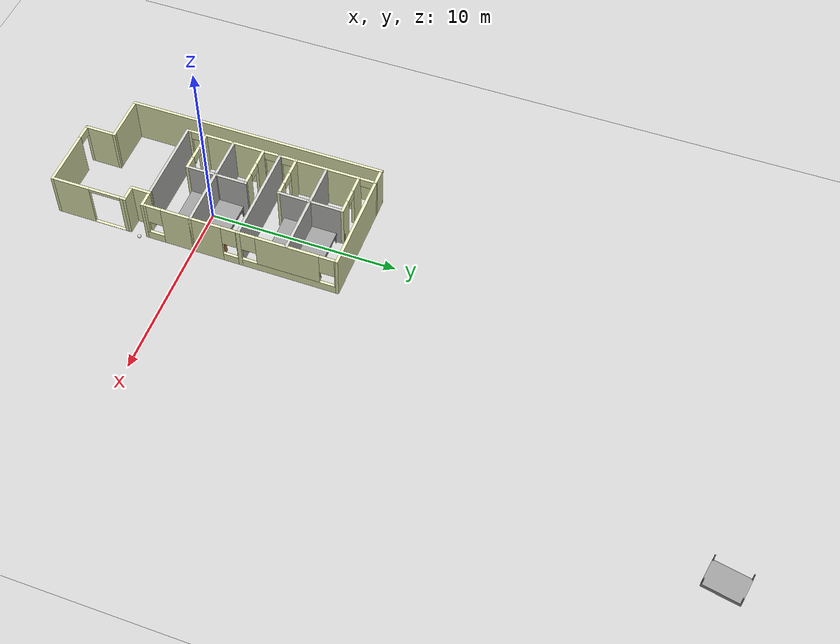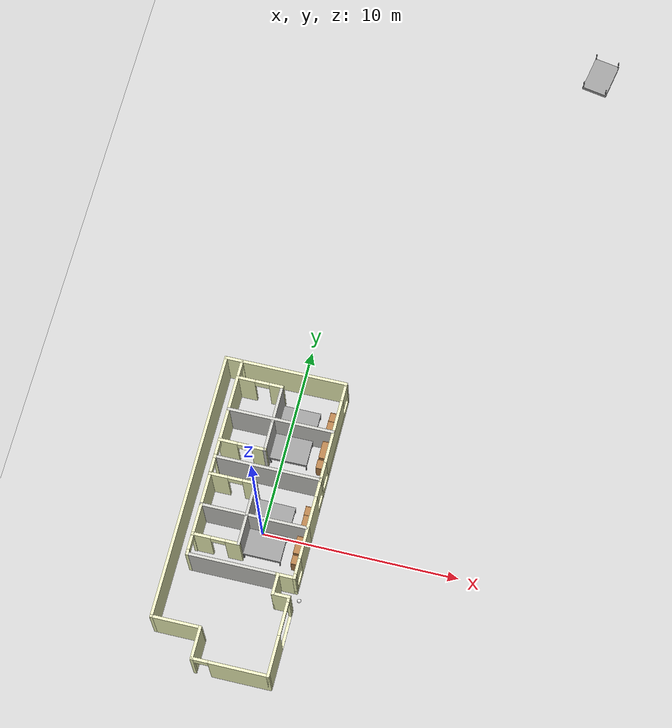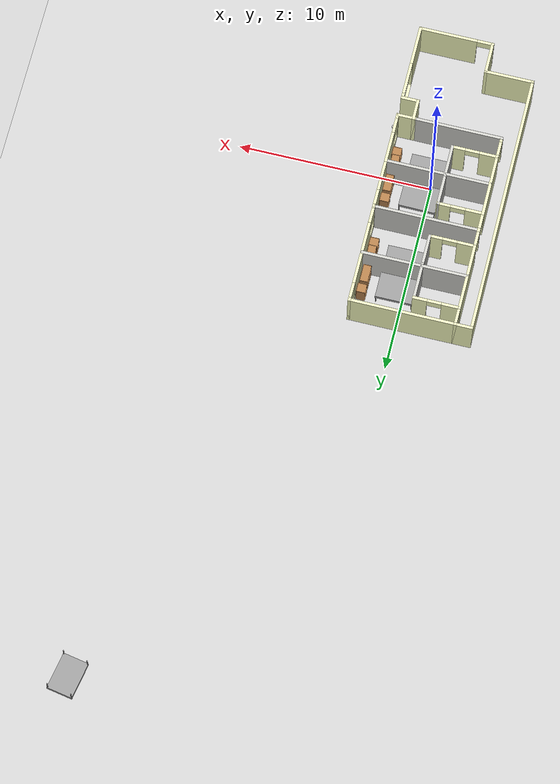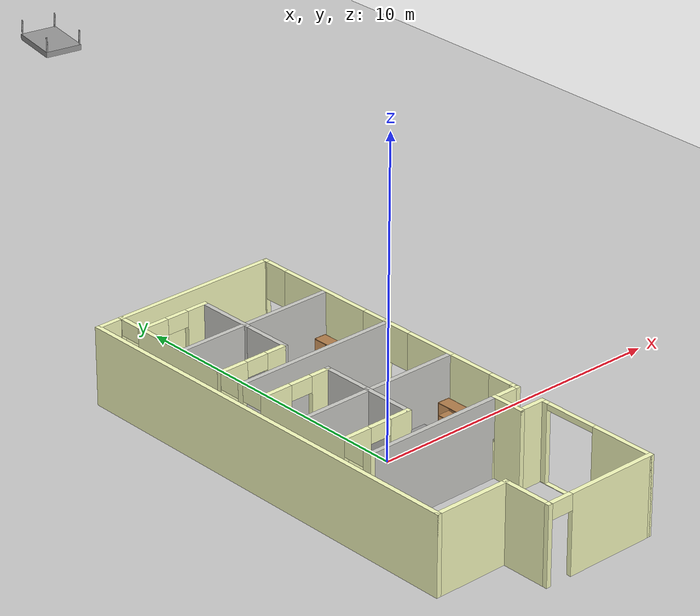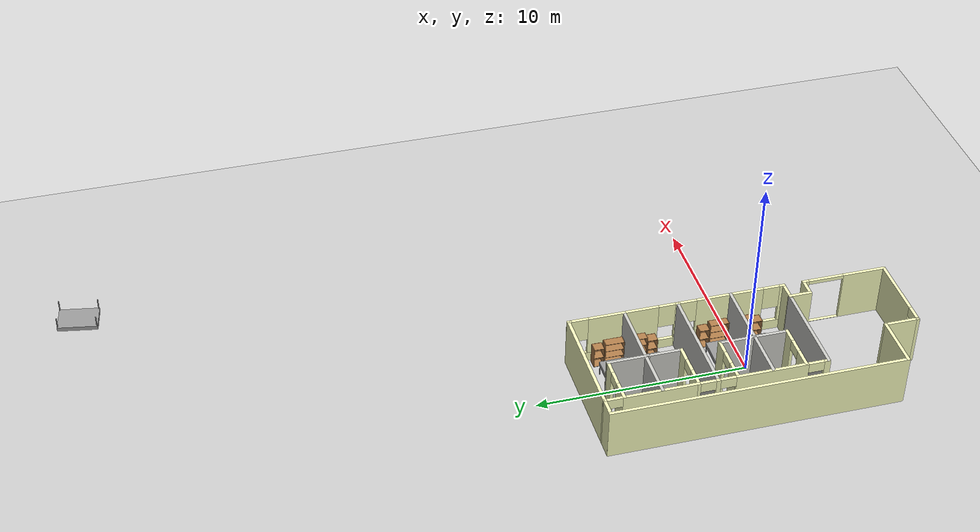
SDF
<sdf version="1.6">
 <world name="default">
  <plugin name="hello" filename="libhello.so"/>
  <light name="sun" type="directional">
   <pose>0 0 10 0 -0 0</pose>
   <diffuse>0.8 0.8 0.8 1</diffuse>
   <specular>0.2 0.2 0.2 1</specular>
   <attenuation>
    <range>1000</range>
    <constant>0.9</constant>
    <linear>0.01</linear>
    <quadratic>0.001</quadratic>
   </attenuation>
   <direction>-0.5 0.1 -0.9</direction>
  </light>
  <model name="ground_plane">
   <static>1</static>
   <link name="link">
    <collision name="collision">
     <geometry><plane><normal>0 0 1</normal><size>100 100</size></plane></geometry>
     <surface>
      <contact><collide_bitmask>65535</collide_bitmask></contact>
      <friction><ode><mu>100</mu><mu2>50</mu2></ode></friction>
     </surface>
    </collision>
    <visual name="visual">
     <cast_shadows>0</cast_shadows>
     <geometry><plane><normal>0 0 1</normal><size>100 100</size></plane></geometry>
     <material>
      <script><uri>file://media/materials/scripts/gazebo.material</uri><name>Gazebo/Grey</name></script>
     </material>
    </visual>
   </link>
  </model>
  <gravity>0 0 -9.8</gravity>
  <magnetic_field>6e-06 2.3e-05 -4.2e-05</magnetic_field>
  <atmosphere type="adiabatic"/>
  <physics name="default_physics" default="0" type="ode">
   <max_step_size>0.001</max_step_size>
   <real_time_factor>1</real_time_factor>
   <real_time_update_rate>1000</real_time_update_rate>
  </physics>
  <scene><ambient>0.4 0.4 0.4 1</ambient><background>0.7 0.7 0.7 1</background><shadows>1</shadows></scene>
  <spherical_coordinates>
   <surface_model>EARTH_WGS84</surface_model>
   <latitude_deg>0</latitude_deg>
   <longitude_deg>0</longitude_deg>
   <elevation>0</elevation>
   <heading_deg>0</heading_deg>
  </spherical_coordinates>
  <model name="bed">
   <pose>0.544611 0.514424 0.569416 1e-06 0 -0.013106</pose>
   <link name="link_0">
    <pose>-0.152081 0.31625 0.061083 0 -0 0</pose>
    <inertial>
     <mass>1</mass>
     <inertia>
      <ixx>0.166667</ixx>
      <ixy>0</ixy>
      <ixz>0</ixz>
      <iyy>0.166667</iyy>
      <iyz>0</iyz>
      <izz>0.166667</izz>
     </inertia>
    </inertial>
    <visual name="visual">
     <geometry><box><size>1.905 1.345 0.205</size></box></geometry>
     <material>
      <lighting>1</lighting>
      <script><uri>file://media/materials/scripts/gazebo.material</uri><name>Gazebo/Grey</name></script>
      <shader type="pixel"><normal_map>__default__</normal_map></shader>
      <ambient>0.3 0.3 0.3 1</ambient>
      <diffuse>0.7 0.7 0.7 1</diffuse>
      <specular>0.01 0.01 0.01 1</specular>
      <emissive>0 0 0 1</emissive>
     </material>
    </visual>
    <collision name="collision">
     <geometry><box><size>1.905 1.345 0.205</size></box></geometry>
     <surface>
      <friction>
       <ode><mu>1</mu><mu2>1</mu2><fdir1>0 0 0</fdir1><slip1>0</slip1><slip2>0</slip2></ode>
       <torsional>
        <coefficient>1</coefficient>
        <patch_radius>0</patch_radius>
        <surface_radius>0</surface_radius>
        <use_patch_radius>1</use_patch_radius>
        <ode><slip>0</slip></ode>
       </torsional>
      </friction>
      <bounce><restitution_coefficient>0</restitution_coefficient><threshold>1e+06</threshold></bounce>
      <contact>
       <collide_without_contact>0</collide_without_contact>
       <collide_without_contact_bitmask>1</collide_without_contact_bitmask>
       <collide_bitmask>1</collide_bitmask>
       <ode>
        <soft_cfm>0</soft_cfm>
        <soft_erp>0.2</soft_erp>
        <kp>1e+13</kp>
        <kd>1</kd>
        <max_vel>0.01</max_vel>
        <min_depth>0</min_depth>
       </ode>
       <bullet>
        <split_impulse>1</split_impulse>
        <split_impulse_penetration_threshold>-0.01</split_impulse_penetration_threshold>
        <soft_cfm>0</soft_cfm>
        <soft_erp>0.2</soft_erp>
        <kp>1e+13</kp>
        <kd>1</kd>
       </bullet>
      </contact>
     </surface>
    </collision>
   </link>
   <link name="link_1">
    <pose>0.760419 0.94875 -0.305417 0 -0 0</pose>
    <inertial>
     <mass>1</mass>
     <inertia><ixx>0.145833</ixx><ixy>0</ixy><ixz>0</ixz><iyy>0.145833</iyy><iyz>0</iyz><izz>0.125</izz></inertia>
    </inertial>
    <visual name="visual">
     <geometry><cylinder><radius>0.026479</radius><length>0.528</length></cylinder></geometry>
     <material>
      <lighting>1</lighting>
      <script><uri>file://media/materials/scripts/gazebo.material</uri><name>Gazebo/Grey</name></script>
      <shader type="pixel"><normal_map>__default__</normal_map></shader>
      <ambient>0.3 0.3 0.3 1</ambient>
      <diffuse>0.7 0.7 0.7 1</diffuse>
      <specular>0.01 0.01 0.01 1</specular>
      <emissive>0 0 0 1</emissive>
     </material>
    </visual>
    <collision name="collision">
     <geometry><cylinder><radius>0.026479</radius><length>0.528</length></cylinder></geometry>
     <surface>
      <friction>
       <ode><mu>1</mu><mu2>1</mu2><fdir1>0 0 0</fdir1><slip1>0</slip1><slip2>0</slip2></ode>
       <torsional>
        <coefficient>1</coefficient>
        <patch_radius>0</patch_radius>
        <surface_radius>0</surface_radius>
        <use_patch_radius>1</use_patch_radius>
        <ode><slip>0</slip></ode>
       </torsional>
      </friction>
      <bounce><restitution_coefficient>0</restitution_coefficient><threshold>1e+06</threshold></bounce>
      <contact>
       <collide_without_contact>0</collide_without_contact>
       <collide_without_contact_bitmask>1</collide_without_contact_bitmask>
       <collide_bitmask>1</collide_bitmask>
       <ode>
        <soft_cfm>0</soft_cfm>
        <soft_erp>0.2</soft_erp>
        <kp>1e+13</kp>
        <kd>1</kd>
        <max_vel>0.01</max_vel>
        <min_depth>0</min_depth>
       </ode>
       <bullet>
        <split_impulse>1</split_impulse>
        <split_impulse_penetration_threshold>-0.01</split_impulse_penetration_threshold>
        <soft_cfm>0</soft_cfm>
        <soft_erp>0.2</soft_erp>
        <kp>1e+13</kp>
        <kd>1</kd>
       </bullet>
      </contact>
     </surface>
    </collision>
   </link>
   <link name="link_1_clone">
    <pose>0.760419 -0.31625 -0.305417 0 -0 0</pose>
    <inertial>
     <mass>1</mass>
     <inertia><ixx>0.145833</ixx><ixy>0</ixy><ixz>0</ixz><iyy>0.145833</iyy><iyz>0</iyz><izz>0.125</izz></inertia>
    </inertial>
    <visual name="visual">
     <geometry><cylinder><radius>0.026479</radius><length>0.528</length></cylinder></geometry>
     <material>
      <lighting>1</lighting>
      <script><uri>file://media/materials/scripts/gazebo.material</uri><name>Gazebo/Grey</name></script>
      <shader type="pixel"><normal_map>__default__</normal_map></shader>
      <ambient>0.3 0.3 0.3 1</ambient>
      <diffuse>0.7 0.7 0.7 1</diffuse>
      <specular>0.01 0.01 0.01 1</specular>
      <emissive>0 0 0 1</emissive>
     </material>
    </visual>
    <collision name="collision">
     <geometry><cylinder><radius>0.026479</radius><length>0.528</length></cylinder></geometry>
     <surface>
      <friction>
       <ode><mu>1</mu><mu2>1</mu2><fdir1>0 0 0</fdir1><slip1>0</slip1><slip2>0</slip2></ode>
       <torsional>
        <coefficient>1</coefficient>
        <patch_radius>0</patch_radius>
        <surface_radius>0</surface_radius>
        <use_patch_radius>1</use_patch_radius>
        <ode><slip>0</slip></ode>
       </torsional>
      </friction>
      <bounce><restitution_coefficient>0</restitution_coefficient><threshold>1e+06</threshold></bounce>
      <contact>
       <collide_without_contact>0</collide_without_contact>
       <collide_without_contact_bitmask>1</collide_without_contact_bitmask>
       <collide_bitmask>1</collide_bitmask>
       <ode>
        <soft_cfm>0</soft_cfm>
        <soft_erp>0.2</soft_erp>
        <kp>1e+13</kp>
        <kd>1</kd>
        <max_vel>0.01</max_vel>
        <min_depth>0</min_depth>
       </ode>
       <bullet>
        <split_impulse>1</split_impulse>
        <split_impulse_penetration_threshold>-0.01</split_impulse_penetration_threshold>
        <soft_cfm>0</soft_cfm>
        <soft_erp>0.2</soft_erp>
        <kp>1e+13</kp>
        <kd>1</kd>
       </bullet>
      </contact>
     </surface>
    </collision>
   </link>
   <link name="link_1_clone_clone">
    <pose>-1.06458 0.94875 -0.305417 0 -0 0</pose>
    <inertial>
     <mass>1</mass>
     <inertia><ixx>0.145833</ixx><ixy>0</ixy><ixz>0</ixz><iyy>0.145833</iyy><iyz>0</iyz><izz>0.125</izz></inertia>
    </inertial>
    <visual name="visual">
     <geometry><cylinder><radius>0.026479</radius><length>0.528</length></cylinder></geometry>
     <material>
      <lighting>1</lighting>
      <script><uri>file://media/materials/scripts/gazebo.material</uri><name>Gazebo/Grey</name></script>
      <shader type="pixel"><normal_map>__default__</normal_map></shader>
      <ambient>0.3 0.3 0.3 1</ambient>
      <diffuse>0.7 0.7 0.7 1</diffuse>
      <specular>0.01 0.01 0.01 1</specular>
      <emissive>0 0 0 1</emissive>
     </material>
    </visual>
    <collision name="collision">
     <geometry><cylinder><radius>0.026479</radius><length>0.528</length></cylinder></geometry>
     <surface>
      <friction>
       <ode><mu>1</mu><mu2>1</mu2><fdir1>0 0 0</fdir1><slip1>0</slip1><slip2>0</slip2></ode>
       <torsional>
        <coefficient>1</coefficient>
        <patch_radius>0</patch_radius>
        <surface_radius>0</surface_radius>
        <use_patch_radius>1</use_patch_radius>
        <ode><slip>0</slip></ode>
       </torsional>
      </friction>
      <bounce><restitution_coefficient>0</restitution_coefficient><threshold>1e+06</threshold></bounce>
      <contact>
       <collide_without_contact>0</collide_without_contact>
       <collide_without_contact_bitmask>1</collide_without_contact_bitmask>
       <collide_bitmask>1</collide_bitmask>
       <ode>
        <soft_cfm>0</soft_cfm>
        <soft_erp>0.2</soft_erp>
        <kp>1e+13</kp>
        <kd>1</kd>
        <max_vel>0.01</max_vel>
        <min_depth>0</min_depth>
       </ode>
       <bullet>
        <split_impulse>1</split_impulse>
        <split_impulse_penetration_threshold>-0.01</split_impulse_penetration_threshold>
        <soft_cfm>0</soft_cfm>
        <soft_erp>0.2</soft_erp>
        <kp>1e+13</kp>
        <kd>1</kd>
       </bullet>
      </contact>
     </surface>
    </collision>
   </link>
   <link name="link_1_clone_clone_clone">
    <pose>-1.06458 -0.31625 -0.305417 0 -0 0</pose>
    <inertial>
     <mass>1</mass>
     <inertia><ixx>0.145833</ixx><ixy>0</ixy><ixz>0</ixz><iyy>0.145833</iyy><iyz>0</iyz><izz>0.125</izz></inertia>
    </inertial>
    <visual name="visual">
     <geometry><cylinder><radius>0.026479</radius><length>0.528</length></cylinder></geometry>
     <material>
      <lighting>1</lighting>
      <script><uri>file://media/materials/scripts/gazebo.material</uri><name>Gazebo/Grey</name></script>
      <shader type="pixel"><normal_map>__default__</normal_map></shader>
      <ambient>0.3 0.3 0.3 1</ambient>
      <diffuse>0.7 0.7 0.7 1</diffuse>
      <specular>0.01 0.01 0.01 1</specular>
      <emissive>0 0 0 1</emissive>
     </material>
    </visual>
    <collision name="collision">
     <geometry><cylinder><radius>0.026479</radius><length>0.528</length></cylinder></geometry>
     <surface>
      <friction>
       <ode><mu>1</mu><mu2>1</mu2><fdir1>0 0 0</fdir1><slip1>0</slip1><slip2>0</slip2></ode>
       <torsional>
        <coefficient>1</coefficient>
        <patch_radius>0</patch_radius>
        <surface_radius>0</surface_radius>
        <use_patch_radius>1</use_patch_radius>
        <ode><slip>0</slip></ode>
       </torsional>
      </friction>
      <bounce><restitution_coefficient>0</restitution_coefficient><threshold>1e+06</threshold></bounce>
      <contact>
       <collide_without_contact>0</collide_without_contact>
       <collide_without_contact_bitmask>1</collide_without_contact_bitmask>
       <collide_bitmask>1</collide_bitmask>
       <ode>
        <soft_cfm>0</soft_cfm>
        <soft_erp>0.2</soft_erp>
        <kp>1e+13</kp>
        <kd>1</kd>
        <max_vel>0.01</max_vel>
        <min_depth>0</min_depth>
       </ode>
       <bullet>
        <split_impulse>1</split_impulse>
        <split_impulse_penetration_threshold>-0.01</split_impulse_penetration_threshold>
        <soft_cfm>0</soft_cfm>
        <soft_erp>0.2</soft_erp>
        <kp>1e+13</kp>
        <kd>1</kd>
       </bullet>
      </contact>
     </surface>
    </collision>
   </link>
   <joint name="link_0_JOINT_0" type="fixed">
    <parent>link_0</parent>
    <child>link_1</child>
    <physics>
     <ode><limit><cfm>0</cfm><erp>0.2</erp></limit><suspension><cfm>0</cfm><erp>0.2</erp></suspension></ode>
    </physics>
   </joint>
   <joint name="link_0_JOINT_1" type="fixed">
    <parent>link_0</parent>
    <child>link_1_clone</child>
    <physics>
     <ode><limit><cfm>0</cfm><erp>0.2</erp></limit><suspension><cfm>0</cfm><erp>0.2</erp></suspension></ode>
    </physics>
   </joint>
   <joint name="link_0_JOINT_2" type="fixed">
    <parent>link_0</parent>
    <child>link_1_clone_clone</child>
    <physics>
     <ode><limit><cfm>0</cfm><erp>0.2</erp></limit><suspension><cfm>0</cfm><erp>0.2</erp></suspension></ode>
    </physics>
   </joint>
   <joint name="link_0_JOINT_3" type="fixed">
    <parent>link_0</parent>
    <child>link_1_clone_clone_clone</child>
    <pose>-0.01 0 0 0 -0 0</pose>
    <physics>
     <ode><limit><cfm>0</cfm><erp>0.2</erp></limit><suspension><cfm>0</cfm><erp>0.2</erp></suspension></ode>
    </physics>
   </joint>
   <static>0</static>
  </model>
  <model name="struc">
   <pose>-0.703267 0.14082 1e-06 0 -0.006238 0</pose>
   <link name="Wall_10">
    <collision name="Wall_10_Collision">
     <geometry><box><size>1.715 0.15 2.5</size></box></geometry>
     <pose>0 0 1.25 0 -0 0</pose>
    </collision>
    <visual name="Wall_10_Visual">
     <pose>0 0 1.25 0 -0 0</pose>
     <geometry><box><size>1.715 0.15 2.5</size></box></geometry>
     <material>
      <script><uri>file://media/materials/scripts/gazebo.material</uri><name>Gazebo/Grey</name></script>
      <ambient>0.980392 1 0.752941 1</ambient>
     </material>
     <meta><layer>0</layer></meta>
    </visual>
    <pose>-0.669906 -6.90644 0 0 -0 1.57083</pose>
   </link>
   <link name="Wall_14">
    <pose>1.21509 -7.68894 0 0 0 -3.4e-05</pose>
    <visual name="Wall_14_Visual_0">
     <pose>-1.88496 0 1.25 0 -0 0</pose>
     <geometry><box><size>0.150071 0.15 2.5</size></box></geometry>
     <material>
      <script><uri>file://media/materials/scripts/gazebo.material</uri><name>Gazebo/Grey</name></script>
      <ambient>0.980392 1 0.752941 1</ambient>
     </material>
     <meta><layer>0</layer></meta>
    </visual>
    <collision name="Wall_14_Collision_0">
     <geometry><box><size>0.150071 0.15 2.5</size></box></geometry>
     <pose>-1.88496 0 1.25 0 -0 0</pose>
    </collision>
    <visual name="Wall_14_Visual_1">
     <pose>0.442536 0 1.25 0 -0 0</pose>
     <geometry><box><size>3.03493 0.15 2.5</size></box></geometry>
     <material>
      <script><uri>file://media/materials/scripts/gazebo.material</uri><name>Gazebo/Grey</name></script>
      <ambient>0.980392 1 0.752941 1</ambient>
     </material>
     <meta><layer>0</layer></meta>
    </visual>
    <collision name="Wall_14_Collision_1">
     <geometry><box><size>3.03493 0.15 2.5</size></box></geometry>
     <pose>0.442536 0 1.25 0 -0 0</pose>
    </collision>
    <visual name="Wall_14_Visual_2">
     <pose>-1.44243 0 2.25 0 -0 0</pose>
     <geometry><box><size>0.735 0.15 0.5</size></box></geometry>
     <material>
      <script><uri>file://media/materials/scripts/gazebo.material</uri><name>Gazebo/Grey</name></script>
      <ambient>0.980392 1 0.752941 1</ambient>
     </material>
     <meta><layer>0</layer></meta>
    </visual>
    <collision name="Wall_14_Collision_2">
     <geometry><box><size>0.735 0.15 0.5</size></box></geometry>
     <pose>-1.44243 0 2.25 0 -0 0</pose>
    </collision>
   </link>
   <link name="Wall_16">
    <pose>3.10006 -5.684 0 0 -0 1.5708</pose>
    <visual name="Wall_16_Visual_0">
     <pose>-1.02051 0 1.25 0 -0 0</pose>
     <geometry><box><size>2.11899 0.15 2.5</size></box></geometry>
     <material>
      <script><uri>file://media/materials/scripts/gazebo.material</uri><name>Gazebo/Grey</name></script>
      <ambient>0.980392 1 0.752941 1</ambient>
     </material>
     <meta><layer>0</layer></meta>
    </visual>
    <collision name="Wall_16_Collision_0">
     <geometry><box><size>2.11899 0.15 2.5</size></box></geometry>
     <pose>-1.02051 0 1.25 0 -0 0</pose>
    </collision>
    <visual name="Wall_16_Visual_1">
     <pose>1.05949 0 0.0075 0 -0 0</pose>
     <geometry><box><size>2.04101 0.15 0.015</size></box></geometry>
     <material>
      <script><uri>file://media/materials/scripts/gazebo.material</uri><name>Gazebo/Grey</name></script>
      <ambient>0.980392 1 0.752941 1</ambient>
     </material>
     <meta><layer>0</layer></meta>
    </visual>
    <collision name="Wall_16_Collision_1">
     <geometry><box><size>2.04101 0.15 0.015</size></box></geometry>
     <pose>1.05949 0 0.0075 0 -0 0</pose>
    </collision>
    <visual name="Wall_16_Visual_2">
     <pose>1.91449 0 1.2575 0 -0 0</pose>
     <geometry><box><size>0.331011 0.15 2.485</size></box></geometry>
     <material>
      <script><uri>file://media/materials/scripts/gazebo.material</uri><name>Gazebo/Grey</name></script>
      <ambient>0.980392 1 0.752941 1</ambient>
     </material>
     <meta><layer>0</layer></meta>
    </visual>
    <collision name="Wall_16_Collision_2">
     <geometry><box><size>0.331011 0.15 2.485</size></box></geometry>
     <pose>1.91449 0 1.2575 0 -0 0</pose>
    </collision>
    <visual name="Wall_16_Visual_3">
     <pose>0.893989 0 2.4075 0 -0 0</pose>
     <geometry><box><size>1.71 0.15 0.185</size></box></geometry>
     <material>
      <script><uri>file://media/materials/scripts/gazebo.material</uri><name>Gazebo/Grey</name></script>
      <ambient>0.980392 1 0.752941 1</ambient>
     </material>
     <meta><layer>0</layer></meta>
    </visual>
    <collision name="Wall_16_Collision_3">
     <geometry><box><size>1.71 0.15 0.185</size></box></geometry>
     <pose>0.893989 0 2.4075 0 -0 0</pose>
    </collision>
   </link>
   <link name="Wall_22">
    <collision name="Wall_22_Collision">
     <geometry><box><size>0.950805 0.15 2.5</size></box></geometry>
     <pose>0 0 1.25 0 -0 0</pose>
    </collision>
    <visual name="Wall_22_Visual">
     <pose>0 0 1.25 0 -0 0</pose>
     <geometry><box><size>0.950805 0.15 2.5</size></box></geometry>
     <material>
      <script><uri>file://media/materials/scripts/gazebo.material</uri><name>Gazebo/Grey</name></script>
      <ambient>0.980392 1 0.752941 1</ambient>
     </material>
     <meta><layer>0</layer></meta>
    </visual>
    <pose>2.69966 -3.679 0 0 -0 3.14159</pose>
   </link>
   <link name="Wall_24">
    <collision name="Wall_24_Collision">
     <geometry><box><size>1.135 0.15 2.5</size></box></geometry>
     <pose>0 0 1.253 0 -0 0</pose>
    </collision>
    <visual name="Wall_24_Visual">
     <pose>0 0 1.253 0 -0 0</pose>
     <geometry><box><size>1.135 0.15 2.5</size></box></geometry>
     <material>
      <script><uri>file://media/materials/scripts/gazebo.material</uri><name>Gazebo/Grey</name></script>
      <ambient>0.980392 1 0.752941 1</ambient>
     </material>
     <meta><layer>0</layer></meta>
    </visual>
    <pose>2.29066 -3.1865 0 0 -0 1.5708</pose>
   </link>
   <link name="Wall_28">
    <collision name="Wall_28_Collision">
     <geometry><box><size>2.58426 0.15 2.5</size></box></geometry>
     <pose>0 0 1.25 0 -0 0</pose>
    </collision>
    <visual name="Wall_28_Visual">
     <pose>0 0 1.25 0 -0 0</pose>
     <geometry><box><size>2.58426 0.15 2.5</size></box></geometry>
     <material>
      <script><uri>file://media/materials/scripts/gazebo.material</uri><name>Gazebo/Grey</name></script>
      <ambient>0.980392 1 0.752941 1</ambient>
     </material>
     <meta><layer>0</layer></meta>
    </visual>
    <pose>-1.88706 -6.124 0 0 -0 3.14159</pose>
   </link>
   <link name="Wall_30">
    <collision name="Wall_30_Collision">
     <geometry><box><size>13.963 0.15 2.5</size></box></geometry>
     <pose>0 0 1.25 0 -0 0</pose>
    </collision>
    <visual name="Wall_30_Visual">
     <pose>0 0 1.25 0 -0 0</pose>
     <geometry><box><size>13.963 0.15 2.5</size></box></geometry>
     <material>
      <script><uri>file://media/materials/scripts/gazebo.material</uri><name>Gazebo/Grey</name></script>
      <ambient>0.980392 1 0.752941 1</ambient>
     </material>
     <meta><layer>0</layer></meta>
    </visual>
    <pose>-3.106 0.782499 0 0 -0 1.57079</pose>
   </link>
   <link name="Wall_32">
    <collision name="Wall_32_Collision">
     <geometry><box><size>0.98 0.15 2.5</size></box></geometry>
     <pose>0 0 1.25 0 -0 0</pose>
    </collision>
    <visual name="Wall_32_Visual">
     <pose>0 0 1.25 0 -0 0</pose>
     <geometry><box><size>0.98 0.15 2.5</size></box></geometry>
     <material>
      <script><uri>file://media/materials/scripts/gazebo.material</uri><name>Gazebo/Grey</name></script>
      <ambient>0.980392 1 0.752941 1</ambient>
     </material>
     <meta><layer>0</layer></meta>
    </visual>
    <pose>-2.69094 7.689 0 0 -0 0</pose>
   </link>
   <link name="Wall_34">
    <pose>-2.27594 2.4975 0 0 0 -1.5708</pose>
    <visual name="Wall_34_Visual_0">
     <pose>-5.18585 0 1.25 0 -0 0</pose>
     <geometry><box><size>0.161301 0.15 2.5</size></box></geometry>
     <material>
      <script><uri>file://media/materials/scripts/gazebo.material</uri><name>Gazebo/Grey</name></script>
      <ambient>0.980392 1 0.752941 1</ambient>
     </material>
     <meta><layer>0</layer></meta>
    </visual>
    <collision name="Wall_34_Collision_0">
     <geometry><box><size>0.161301 0.15 2.5</size></box></geometry>
     <pose>-5.18585 0 1.25 0 -0 0</pose>
    </collision>
    <visual name="Wall_34_Visual_1">
     <pose>-2.59577 0 1.25 0 -0 0</pose>
     <geometry><box><size>3.54886 0.15 2.5</size></box></geometry>
     <material>
      <script><uri>file://media/materials/scripts/gazebo.material</uri><name>Gazebo/Grey</name></script>
      <ambient>0.980392 1 0.752941 1</ambient>
     </material>
     <meta><layer>0</layer></meta>
    </visual>
    <collision name="Wall_34_Collision_1">
     <geometry><box><size>3.54886 0.15 2.5</size></box></geometry>
     <pose>-2.59577 0 1.25 0 -0 0</pose>
    </collision>
    <visual name="Wall_34_Visual_2">
     <pose>0.01567 0 1.25 0 -0 0</pose>
     <geometry><box><size>0.204017 0.15 2.5</size></box></geometry>
     <material>
      <script><uri>file://media/materials/scripts/gazebo.material</uri><name>Gazebo/Grey</name></script>
      <ambient>0.980392 1 0.752941 1</ambient>
     </material>
     <meta><layer>0</layer></meta>
    </visual>
    <collision name="Wall_34_Collision_2">
     <geometry><box><size>0.204017 0.15 2.5</size></box></geometry>
     <pose>0.01567 0 1.25 0 -0 0</pose>
    </collision>
    <visual name="Wall_34_Visual_3">
     <pose>2.54627 0 1.25 0 -0 0</pose>
     <geometry><box><size>3.38719 0.15 2.5</size></box></geometry>
     <material>
      <script><uri>file://media/materials/scripts/gazebo.material</uri><name>Gazebo/Grey</name></script>
      <ambient>0.980392 1 0.752941 1</ambient>
     </material>
     <meta><layer>0</layer></meta>
    </visual>
    <collision name="Wall_34_Collision_3">
     <geometry><box><size>3.38719 0.15 2.5</size></box></geometry>
     <pose>2.54627 0 1.25 0 -0 0</pose>
    </collision>
    <visual name="Wall_34_Visual_4">
     <pose>5.12069 0 1.25 0 -0 0</pose>
     <geometry><box><size>0.291637 0.15 2.5</size></box></geometry>
     <material>
      <script><uri>file://media/materials/scripts/gazebo.material</uri><name>Gazebo/Grey</name></script>
      <ambient>0.980392 1 0.752941 1</ambient>
     </material>
     <meta><layer>0</layer></meta>
    </visual>
    <collision name="Wall_34_Collision_4">
     <geometry><box><size>0.291637 0.15 2.5</size></box></geometry>
     <pose>5.12069 0 1.25 0 -0 0</pose>
    </collision>
    <visual name="Wall_34_Visual_5">
     <pose>-4.7377 0 2.25 0 -0 0</pose>
     <geometry><box><size>0.735 0.15 0.5</size></box></geometry>
     <material>
      <script><uri>file://media/materials/scripts/gazebo.material</uri><name>Gazebo/Grey</name></script>
      <ambient>0.980392 1 0.752941 1</ambient>
     </material>
     <meta><layer>0</layer></meta>
    </visual>
    <collision name="Wall_34_Collision_5">
     <geometry><box><size>0.735 0.15 0.5</size></box></geometry>
     <pose>-4.7377 0 2.25 0 -0 0</pose>
    </collision>
    <visual name="Wall_34_Visual_6">
     <pose>-0.453839 0 2.25 0 -0 0</pose>
     <geometry><box><size>0.735 0.15 0.5</size></box></geometry>
     <material>
      <script><uri>file://media/materials/scripts/gazebo.material</uri><name>Gazebo/Grey</name></script>
      <ambient>0.980392 1 0.752941 1</ambient>
     </material>
     <meta><layer>0</layer></meta>
    </visual>
    <collision name="Wall_34_Collision_6">
     <geometry><box><size>0.735 0.15 0.5</size></box></geometry>
     <pose>-0.453839 0 2.25 0 -0 0</pose>
    </collision>
    <visual name="Wall_34_Visual_7">
     <pose>0.485178 0 2.25 0 -0 0</pose>
     <geometry><box><size>0.735 0.15 0.5</size></box></geometry>
     <material>
      <script><uri>file://media/materials/scripts/gazebo.material</uri><name>Gazebo/Grey</name></script>
      <ambient>0.980392 1 0.752941 1</ambient>
     </material>
     <meta><layer>0</layer></meta>
    </visual>
    <collision name="Wall_34_Collision_7">
     <geometry><box><size>0.735 0.15 0.5</size></box></geometry>
     <pose>0.485178 0 2.25 0 -0 0</pose>
    </collision>
    <visual name="Wall_34_Visual_8">
     <pose>4.60737 0 2.25 0 -0 0</pose>
     <geometry><box><size>0.735 0.15 0.5</size></box></geometry>
     <material>
      <script><uri>file://media/materials/scripts/gazebo.material</uri><name>Gazebo/Grey</name></script>
      <ambient>0.980392 1 0.752941 1</ambient>
     </material>
     <meta><layer>0</layer></meta>
    </visual>
    <collision name="Wall_34_Collision_8">
     <geometry><box><size>0.735 0.15 0.5</size></box></geometry>
     <pose>4.60737 0 2.25 0 -0 0</pose>
    </collision>
   </link>
   <link name="Wall_36">
    <collision name="Wall_36_Collision">
     <geometry><box><size>4.663 0.15 2.5</size></box></geometry>
     <pose>0 0 1.25 0 -0 0</pose>
    </collision>
    <visual name="Wall_36_Visual">
     <pose>0 0 1.25 0 -0 0</pose>
     <geometry><box><size>4.663 0.15 2.5</size></box></geometry>
     <material>
      <script><uri>file://media/materials/scripts/gazebo.material</uri><name>Gazebo/CeilingTiled</name></script>
      <ambient>0.980392 1 0.752941 1</ambient>
     </material>
     <meta><layer>0</layer></meta>
    </visual>
    <pose>-0.019435 -2.694 0 0 -0 0</pose>
   </link>
   <link name="Wall_39">
    <collision name="Wall_39_Collision">
     <geometry><box><size>5.512 0.15 2.5</size></box></geometry>
     <pose>0 0 1.25 0 -0 0</pose>
    </collision>
    <visual name="Wall_39_Visual">
     <pose>0 0 1.25 0 -0 0</pose>
     <geometry><box><size>5.512 0.15 2.5</size></box></geometry>
     <material>
      <script><uri>file://media/materials/scripts/gazebo.material</uri><name>Gazebo/CeilingTiled</name></script>
      <ambient>0.980392 1 0.752941 1</ambient>
     </material>
     <meta><layer>0</layer></meta>
    </visual>
    <pose>0.425065 -0.094001 0 0 -0 0</pose>
   </link>
   <link name="Wall_41">
    <pose>3.10607 -1.394 0 0 0 -1.5708</pose>
    <visual name="Wall_41_Visual_0">
     <pose>-0.542032 0 1.25 0 -0 0</pose>
     <geometry><box><size>1.66593 0.15 2.5</size></box></geometry>
     <material>
      <script><uri>file://media/materials/scripts/gazebo.material</uri><name>Gazebo/Grey</name></script>
      <ambient>0.980392 1 0.752941 1</ambient>
     </material>
     <meta><layer>0</layer></meta>
    </visual>
    <collision name="Wall_41_Collision_0">
     <geometry><box><size>1.66593 0.15 2.5</size></box></geometry>
     <pose>-0.542032 0 1.25 0 -0 0</pose>
    </collision>
    <visual name="Wall_41_Visual_1">
     <pose>0.832968 0 0.25 0 -0 0</pose>
     <geometry><box><size>1.08407 0.15 0.5</size></box></geometry>
     <material>
      <script><uri>file://media/materials/scripts/gazebo.material</uri><name>Gazebo/Grey</name></script>
      <ambient>0.980392 1 0.752941 1</ambient>
     </material>
     <meta><layer>0</layer></meta>
    </visual>
    <collision name="Wall_41_Collision_1">
     <geometry><box><size>1.08407 0.15 0.5</size></box></geometry>
     <pose>0.832968 0 0.25 0 -0 0</pose>
    </collision>
    <visual name="Wall_41_Visual_2">
     <pose>1.23297 0 1.5 0 -0 0</pose>
     <geometry><box><size>0.284065 0.15 2</size></box></geometry>
     <material>
      <script><uri>file://media/materials/scripts/gazebo.material</uri><name>Gazebo/Grey</name></script>
      <ambient>0.980392 1 0.752941 1</ambient>
     </material>
     <meta><layer>0</layer></meta>
    </visual>
    <collision name="Wall_41_Collision_2">
     <geometry><box><size>0.284065 0.15 2</size></box></geometry>
     <pose>1.23297 0 1.5 0 -0 0</pose>
    </collision>
    <visual name="Wall_41_Visual_3">
     <pose>0.690935 0 1.9 0 -0 0</pose>
     <geometry><box><size>0.8 0.15 1.2</size></box></geometry>
     <material>
      <script><uri>file://media/materials/scripts/gazebo.material</uri><name>Gazebo/Grey</name></script>
      <ambient>0.980392 1 0.752941 1</ambient>
     </material>
     <meta><layer>0</layer></meta>
    </visual>
    <collision name="Wall_41_Collision_3">
     <geometry><box><size>0.8 0.15 1.2</size></box></geometry>
     <pose>0.690935 0 1.9 0 -0 0</pose>
    </collision>
   </link>
   <link name="Wall_43">
    <collision name="Wall_43_Collision">
     <geometry><box><size>1.019 0.15 2.5</size></box></geometry>
     <pose>0 0 1.25 0 -0 0</pose>
    </collision>
    <visual name="Wall_43_Visual">
     <pose>0 0 1.25 0 -0 0</pose>
     <geometry><box><size>1.019 0.15 2.5</size></box></geometry>
     <material>
      <script><uri>file://media/materials/scripts/gazebo.material</uri><name>Gazebo/Grey</name></script>
      <ambient>0.980392 1 0.752941 1</ambient>
     </material>
     <meta><layer>0</layer></meta>
    </visual>
    <pose>2.67157 -2.694 0 0 -0 0</pose>
   </link>
   <link name="Wall_45">
    <collision name="Wall_45_Collision">
     <geometry><box><size>5.512 0.15 2.5</size></box></geometry>
     <pose>0 0 1.25 0 -0 0</pose>
    </collision>
    <visual name="Wall_45_Visual">
     <pose>0 0 1.25 0 -0 0</pose>
     <geometry><box><size>5.512 0.15 2.5</size></box></geometry>
     <material>
      <script><uri>file://media/materials/scripts/gazebo.material</uri><name>Gazebo/CeilingTiled</name></script>
      <ambient>0.980392 1 0.752941 1</ambient>
     </material>
     <meta><layer>0</layer></meta>
    </visual>
    <pose>0.418065 2.479 0 0 -0 0</pose>
   </link>
   <link name="Wall_49">
    <pose>3.10607 1.184 0 0 -0 1.5708</pose>
    <visual name="Wall_49_Visual_0">
     <pose>-0.485277 0 1.25 0 -0 0</pose>
     <geometry><box><size>1.73544 0.15 2.5</size></box></geometry>
     <material>
      <script><uri>file://media/materials/scripts/gazebo.material</uri><name>Gazebo/Grey</name></script>
      <ambient>0.980392 1 0.752941 1</ambient>
     </material>
     <meta><layer>0</layer></meta>
    </visual>
    <collision name="Wall_49_Collision_0">
     <geometry><box><size>1.73544 0.15 2.5</size></box></geometry>
     <pose>-0.485277 0 1.25 0 -0 0</pose>
    </collision>
    <visual name="Wall_49_Visual_1">
     <pose>0.867722 0 0.25 0 -0 0</pose>
     <geometry><box><size>0.970553 0.15 0.5</size></box></geometry>
     <material>
      <script><uri>file://media/materials/scripts/gazebo.material</uri><name>Gazebo/Grey</name></script>
      <ambient>0.980392 1 0.752941 1</ambient>
     </material>
     <meta><layer>0</layer></meta>
    </visual>
    <collision name="Wall_49_Collision_1">
     <geometry><box><size>0.970553 0.15 0.5</size></box></geometry>
     <pose>0.867722 0 0.25 0 -0 0</pose>
    </collision>
    <visual name="Wall_49_Visual_2">
     <pose>1.26772 0 1.5 0 -0 0</pose>
     <geometry><box><size>0.170553 0.15 2</size></box></geometry>
     <material>
      <script><uri>file://media/materials/scripts/gazebo.material</uri><name>Gazebo/Grey</name></script>
      <ambient>0.980392 1 0.752941 1</ambient>
     </material>
     <meta><layer>0</layer></meta>
    </visual>
    <collision name="Wall_49_Collision_2">
     <geometry><box><size>0.170553 0.15 2</size></box></geometry>
     <pose>1.26772 0 1.5 0 -0 0</pose>
    </collision>
    <visual name="Wall_49_Visual_3">
     <pose>0.782446 0 1.9 0 -0 0</pose>
     <geometry><box><size>0.8 0.15 1.2</size></box></geometry>
     <material>
      <script><uri>file://media/materials/scripts/gazebo.material</uri><name>Gazebo/Grey</name></script>
      <ambient>0.980392 1 0.752941 1</ambient>
     </material>
     <meta><layer>0</layer></meta>
    </visual>
    <collision name="Wall_49_Collision_3">
     <geometry><box><size>0.8 0.15 1.2</size></box></geometry>
     <pose>0.782446 0 1.9 0 -0 0</pose>
    </collision>
   </link>
   <link name="Wall_53">
    <collision name="Wall_53_Collision">
     <geometry><box><size>5.491 0.15 2.5</size></box></geometry>
     <pose>0 0 1.25 0 -0 0</pose>
    </collision>
    <visual name="Wall_53_Visual">
     <pose>0 0 1.25 0 -0 0</pose>
     <geometry><box><size>5.491 0.15 2.5</size></box></geometry>
     <material>
      <script><uri>file://media/materials/scripts/gazebo.material</uri><name>Gazebo/CeilingTiled</name></script>
      <ambient>0.980392 1 0.752941 1</ambient>
     </material>
     <meta><layer>0</layer></meta>
    </visual>
    <pose>0.407566 5.052 0 0 -0 0</pose>
   </link>
   <link name="Wall_55">
    <pose>3.10607 5.0755 0 0 -0 1.5708</pose>
    <visual name="Wall_55_Visual_0">
     <pose>-2.58145 0 1.25 0 -0 0</pose>
     <geometry><box><size>0.214106 0.15 2.5</size></box></geometry>
     <material>
      <script><uri>file://media/materials/scripts/gazebo.material</uri><name>Gazebo/Grey</name></script>
      <ambient>0.980392 1 0.752941 1</ambient>
     </material>
     <meta><layer>0</layer></meta>
    </visual>
    <collision name="Wall_55_Collision_0">
     <geometry><box><size>0.214106 0.15 2.5</size></box></geometry>
     <pose>-2.58145 0 1.25 0 -0 0</pose>
    </collision>
    <visual name="Wall_55_Visual_1">
     <pose>0.107053 0 0.25 0 -0 0</pose>
     <geometry><box><size>5.16289 0.15 0.5</size></box></geometry>
     <material>
      <script><uri>file://media/materials/scripts/gazebo.material</uri><name>Gazebo/Grey</name></script>
      <ambient>0.980392 1 0.752941 1</ambient>
     </material>
     <meta><layer>0</layer></meta>
    </visual>
    <collision name="Wall_55_Collision_1">
     <geometry><box><size>5.16289 0.15 0.5</size></box></geometry>
     <pose>0.107053 0 0.25 0 -0 0</pose>
    </collision>
    <visual name="Wall_55_Visual_2">
     <pose>0.007393 0 1.5 0 -0 0</pose>
     <geometry><box><size>3.36357 0.15 2</size></box></geometry>
     <material>
      <script><uri>file://media/materials/scripts/gazebo.material</uri><name>Gazebo/Grey</name></script>
      <ambient>0.980392 1 0.752941 1</ambient>
     </material>
     <meta><layer>0</layer></meta>
    </visual>
    <collision name="Wall_55_Collision_2">
     <geometry><box><size>3.36357 0.15 2</size></box></geometry>
     <pose>0.007393 0 1.5 0 -0 0</pose>
    </collision>
    <visual name="Wall_55_Visual_3">
     <pose>2.58884 0 1.5 0 -0 0</pose>
     <geometry><box><size>0.19932 0.15 2</size></box></geometry>
     <material>
      <script><uri>file://media/materials/scripts/gazebo.material</uri><name>Gazebo/Grey</name></script>
      <ambient>0.980392 1 0.752941 1</ambient>
     </material>
     <meta><layer>0</layer></meta>
    </visual>
    <collision name="Wall_55_Collision_3">
     <geometry><box><size>0.19932 0.15 2</size></box></geometry>
     <pose>2.58884 0 1.5 0 -0 0</pose>
    </collision>
    <visual name="Wall_55_Visual_4">
     <pose>-2.07439 0 1.9 0 -0 0</pose>
     <geometry><box><size>0.8 0.15 1.2</size></box></geometry>
     <material>
      <script><uri>file://media/materials/scripts/gazebo.material</uri><name>Gazebo/Grey</name></script>
      <ambient>0.980392 1 0.752941 1</ambient>
     </material>
     <meta><layer>0</layer></meta>
    </visual>
    <collision name="Wall_55_Collision_4">
     <geometry><box><size>0.8 0.15 1.2</size></box></geometry>
     <pose>-2.07439 0 1.9 0 -0 0</pose>
    </collision>
    <visual name="Wall_55_Visual_5">
     <pose>2.08918 0 1.9 0 -0 0</pose>
     <geometry><box><size>0.8 0.15 1.2</size></box></geometry>
     <material>
      <script><uri>file://media/materials/scripts/gazebo.material</uri><name>Gazebo/Grey</name></script>
      <ambient>0.980392 1 0.752941 1</ambient>
     </material>
     <meta><layer>0</layer></meta>
    </visual>
    <collision name="Wall_55_Collision_5">
     <geometry><box><size>0.8 0.15 1.2</size></box></geometry>
     <pose>2.08918 0 1.9 0 -0 0</pose>
    </collision>
   </link>
   <link name="Wall_57">
    <collision name="Wall_57_Collision">
     <geometry><box><size>5.532 0.15 2.5</size></box></geometry>
     <pose>0 0 1.25 0 -0 0</pose>
    </collision>
    <visual name="Wall_57_Visual">
     <pose>0 0 1.25 0 -0 0</pose>
     <geometry><box><size>5.532 0.15 2.5</size></box></geometry>
     <material>
      <script><uri>file://media/materials/scripts/gazebo.material</uri><name>Gazebo/Grey</name></script>
      <ambient>0.980392 1 0.752941 1</ambient>
     </material>
     <meta><layer>0</layer></meta>
    </visual>
    <pose>0.415065 7.689 0 0 -0 0</pose>
   </link>
   <link name="Wall_59">
    <pose>-1.11694 1.557 0 0 -0 0</pose>
    <visual name="Wall_59_Visual_0">
     <pose>-0.737383 0 1.25 0 -0 0</pose>
     <geometry><box><size>0.975234 0.15 2.5</size></box></geometry>
     <material>
      <script><uri>file://media/materials/scripts/gazebo.material</uri><name>Gazebo/Grey</name></script>
      <ambient>0.980392 1 0.752941 1</ambient>
     </material>
     <meta><layer>0</layer></meta>
    </visual>
    <collision name="Wall_59_Collision_0">
     <geometry><box><size>0.975234 0.15 2.5</size></box></geometry>
     <pose>-0.737383 0 1.25 0 -0 0</pose>
    </collision>
    <visual name="Wall_59_Visual_1">
     <pose>0.864117 0 1.25 0 -0 0</pose>
     <geometry><box><size>0.721766 0.15 2.5</size></box></geometry>
     <material>
      <script><uri>file://media/materials/scripts/gazebo.material</uri><name>Gazebo/Grey</name></script>
      <ambient>0.980392 1 0.752941 1</ambient>
     </material>
     <meta><layer>0</layer></meta>
    </visual>
    <collision name="Wall_59_Collision_1">
     <geometry><box><size>0.721766 0.15 2.5</size></box></geometry>
     <pose>0.864117 0 1.25 0 -0 0</pose>
    </collision>
    <visual name="Wall_59_Visual_2">
     <pose>0.126734 0 2.25 0 -0 0</pose>
     <geometry><box><size>0.753 0.15 0.5</size></box></geometry>
     <material>
      <script><uri>file://media/materials/scripts/gazebo.material</uri><name>Gazebo/Grey</name></script>
      <ambient>0.980392 1 0.752941 1</ambient>
     </material>
     <meta><layer>0</layer></meta>
    </visual>
    <collision name="Wall_59_Collision_2">
     <geometry><box><size>0.753 0.15 0.5</size></box></geometry>
     <pose>0.126734 0 2.25 0 -0 0</pose>
    </collision>
   </link>
   <link name="Wall_61">
    <collision name="Wall_61_Collision">
     <geometry><box><size>1.75 0.15 2.5</size></box></geometry>
     <pose>0 0 1.25 0 -0 0</pose>
    </collision>
    <visual name="Wall_61_Visual">
     <pose>0 0 1.25 0 -0 0</pose>
     <geometry><box><size>1.75 0.15 2.5</size></box></geometry>
     <material>
      <script><uri>file://media/materials/scripts/gazebo.material</uri><name>Gazebo/CeilingTiled</name></script>
      <ambient>0.980392 1 0.752941 1</ambient>
     </material>
     <meta><layer>0</layer></meta>
    </visual>
    <pose>0.033065 0.756999 0 0 0 -1.5708</pose>
   </link>
   <link name="Wall_63">
    <collision name="Wall_63_Collision">
     <geometry><box><size>1.75 0.15 2.5</size></box></geometry>
     <pose>0 0 1.25 0 -0 0</pose>
    </collision>
    <visual name="Wall_63_Visual">
     <pose>0 0 1.25 0 -0 0</pose>
     <geometry><box><size>1.75 0.15 2.5</size></box></geometry>
     <material>
      <script><uri>file://media/materials/scripts/gazebo.material</uri><name>Gazebo/CeilingTiled</name></script>
      <ambient>0.980392 1 0.752941 1</ambient>
     </material>
     <meta><layer>0</layer></meta>
    </visual>
    <pose>0.033065 -0.843001 0 0 0 -1.5708</pose>
   </link>
   <link name="Wall_65">
    <pose>-1.12143 -1.643 0 0 -0 3.14159</pose>
    <visual name="Wall_65_Visual_0">
     <pose>-0.856038 0 1.25 0 -0 0</pose>
     <geometry><box><size>0.746924 0.15 2.5</size></box></geometry>
     <material>
      <script><uri>file://media/materials/scripts/gazebo.material</uri><name>Gazebo/Grey</name></script>
      <ambient>0.980392 1 0.752941 1</ambient>
     </material>
     <meta><layer>0</layer></meta>
    </visual>
    <collision name="Wall_65_Collision_0">
     <geometry><box><size>0.746924 0.15 2.5</size></box></geometry>
     <pose>-0.856038 0 1.25 0 -0 0</pose>
    </collision>
    <visual name="Wall_65_Visual_1">
     <pose>0.740962 0 1.25 0 -0 0</pose>
     <geometry><box><size>0.977076 0.15 2.5</size></box></geometry>
     <material>
      <script><uri>file://media/materials/scripts/gazebo.material</uri><name>Gazebo/Grey</name></script>
      <ambient>0.980392 1 0.752941 1</ambient>
     </material>
     <meta><layer>0</layer></meta>
    </visual>
    <collision name="Wall_65_Collision_1">
     <geometry><box><size>0.977076 0.15 2.5</size></box></geometry>
     <pose>0.740962 0 1.25 0 -0 0</pose>
    </collision>
    <visual name="Wall_65_Visual_2">
     <pose>-0.115076 0 2.25 0 -0 0</pose>
     <geometry><box><size>0.735 0.15 0.5</size></box></geometry>
     <material>
      <script><uri>file://media/materials/scripts/gazebo.material</uri><name>Gazebo/Grey</name></script>
      <ambient>0.980392 1 0.752941 1</ambient>
     </material>
     <meta><layer>0</layer></meta>
    </visual>
    <collision name="Wall_65_Collision_2">
     <geometry><box><size>0.735 0.15 0.5</size></box></geometry>
     <pose>-0.115076 0 2.25 0 -0 0</pose>
    </collision>
   </link>
   <link name="Wall_69">
    <pose>-1.11993 6.799 0 0 -0 0</pose>
    <visual name="Wall_69_Visual_0">
     <pose>-0.738165 0 1.25 0 -0 0</pose>
     <geometry><box><size>0.973669 0.15 2.5</size></box></geometry>
     <material>
      <script><uri>file://media/materials/scripts/gazebo.material</uri><name>Gazebo/Grey</name></script>
      <ambient>0.980392 1 0.752941 1</ambient>
     </material>
     <meta><layer>0</layer></meta>
    </visual>
    <collision name="Wall_69_Collision_0">
     <geometry><box><size>0.973669 0.15 2.5</size></box></geometry>
     <pose>-0.738165 0 1.25 0 -0 0</pose>
    </collision>
    <visual name="Wall_69_Visual_1">
     <pose>0.854335 0 1.25 0 -0 0</pose>
     <geometry><box><size>0.741331 0.15 2.5</size></box></geometry>
     <material>
      <script><uri>file://media/materials/scripts/gazebo.material</uri><name>Gazebo/Grey</name></script>
      <ambient>0.980392 1 0.752941 1</ambient>
     </material>
     <meta><layer>0</layer></meta>
    </visual>
    <collision name="Wall_69_Collision_1">
     <geometry><box><size>0.741331 0.15 2.5</size></box></geometry>
     <pose>0.854335 0 1.25 0 -0 0</pose>
    </collision>
    <visual name="Wall_69_Visual_2">
     <pose>0.116169 0 2.25 0 -0 0</pose>
     <geometry><box><size>0.735 0.15 0.5</size></box></geometry>
     <material>
      <script><uri>file://media/materials/scripts/gazebo.material</uri><name>Gazebo/Grey</name></script>
      <ambient>0.980392 1 0.752941 1</ambient>
     </material>
     <meta><layer>0</layer></meta>
    </visual>
    <collision name="Wall_69_Collision_2">
     <geometry><box><size>0.735 0.15 0.5</size></box></geometry>
     <pose>0.116169 0 2.25 0 -0 0</pose>
    </collision>
   </link>
   <link name="Wall_72">
    <collision name="Wall_72_Collision">
     <geometry><box><size>2 0.15 2.5</size></box></geometry>
     <pose>0 0 1.25 0 -0 0</pose>
    </collision>
    <visual name="Wall_72_Visual">
     <pose>0 0 1.25 0 -0 0</pose>
     <geometry><box><size>2 0.15 2.5</size></box></geometry>
     <material>
      <script><uri>file://media/materials/scripts/gazebo.material</uri><name>Gazebo/CeilingTiled</name></script>
      <ambient>0.980392 1 0.752941 1</ambient>
     </material>
     <meta><layer>0</layer></meta>
    </visual>
    <pose>0.030065 5.874 0 0 0 -1.5708</pose>
   </link>
   <link name="Wall_74">
    <collision name="Wall_74_Collision">
     <geometry><box><size>1.723 0.15 2.5</size></box></geometry>
     <pose>0 0 1.25 0 -0 0</pose>
    </collision>
    <visual name="Wall_74_Visual">
     <pose>0 0 1.25 0 -0 0</pose>
     <geometry><box><size>1.723 0.15 2.5</size></box></geometry>
     <material>
      <script><uri>file://media/materials/scripts/gazebo.material</uri><name>Gazebo/CeilingTiled</name></script>
      <ambient>0.980392 1 0.752941 1</ambient>
     </material>
     <meta><layer>0</layer></meta>
    </visual>
    <pose>0.030065 4.1625 0 0 0 -1.5708</pose>
   </link>
   <link name="Wall_76">
    <pose>-1.12443 3.376 0 0 -0 0</pose>
    <visual name="Wall_76_Visual_0">
     <pose>-0.740135 0 1.25 0 -0 0</pose>
     <geometry><box><size>0.978729 0.15 2.5</size></box></geometry>
     <material>
      <script><uri>file://media/materials/scripts/gazebo.material</uri><name>Gazebo/Grey</name></script>
      <ambient>0.980392 1 0.752941 1</ambient>
     </material>
     <meta><layer>0</layer></meta>
    </visual>
    <collision name="Wall_76_Collision_0">
     <geometry><box><size>0.978729 0.15 2.5</size></box></geometry>
     <pose>-0.740135 0 1.25 0 -0 0</pose>
    </collision>
    <visual name="Wall_76_Visual_1">
     <pose>0.856865 0 1.25 0 -0 0</pose>
     <geometry><box><size>0.745271 0.15 2.5</size></box></geometry>
     <material>
      <script><uri>file://media/materials/scripts/gazebo.material</uri><name>Gazebo/Grey</name></script>
      <ambient>0.980392 1 0.752941 1</ambient>
     </material>
     <meta><layer>0</layer></meta>
    </visual>
    <collision name="Wall_76_Collision_1">
     <geometry><box><size>0.745271 0.15 2.5</size></box></geometry>
     <pose>0.856865 0 1.25 0 -0 0</pose>
    </collision>
    <visual name="Wall_76_Visual_2">
     <pose>0.116729 0 2.25 0 -0 0</pose>
     <geometry><box><size>0.735 0.15 0.5</size></box></geometry>
     <material>
      <script><uri>file://media/materials/scripts/gazebo.material</uri><name>Gazebo/Grey</name></script>
      <ambient>0.980392 1 0.752941 1</ambient>
     </material>
     <meta><layer>0</layer></meta>
    </visual>
    <collision name="Wall_76_Collision_2">
     <geometry><box><size>0.735 0.15 0.5</size></box></geometry>
     <pose>0.116729 0 2.25 0 -0 0</pose>
    </collision>
   </link>
   <static>1</static>
  </model>
  <model name="bed_clone">
   <link name="link_0">
    <pose>-0.152081 0.31625 0.061083 0 -0 0</pose>
    <inertial>
     <mass>1</mass>
     <inertia>
      <ixx>0.166667</ixx>
      <ixy>0</ixy>
      <ixz>0</ixz>
      <iyy>0.166667</iyy>
      <iyz>0</iyz>
      <izz>0.166667</izz>
     </inertia>
    </inertial>
    <visual name="visual">
     <geometry><box><size>1.905 1.345 0.205</size></box></geometry>
     <material>
      <lighting>1</lighting>
      <script><uri>file://media/materials/scripts/gazebo.material</uri><name>Gazebo/Grey</name></script>
      <shader type="pixel"><normal_map>__default__</normal_map></shader>
      <ambient>0.3 0.3 0.3 1</ambient>
      <diffuse>0.7 0.7 0.7 1</diffuse>
      <specular>0.01 0.01 0.01 1</specular>
      <emissive>0 0 0 1</emissive>
     </material>
    </visual>
    <collision name="collision">
     <geometry><box><size>1.905 1.345 0.205</size></box></geometry>
     <surface>
      <friction>
       <ode><mu>1</mu><mu2>1</mu2><fdir1>0 0 0</fdir1><slip1>0</slip1><slip2>0</slip2></ode>
       <torsional>
        <coefficient>1</coefficient>
        <patch_radius>0</patch_radius>
        <surface_radius>0</surface_radius>
        <use_patch_radius>1</use_patch_radius>
        <ode><slip>0</slip></ode>
       </torsional>
      </friction>
      <bounce><restitution_coefficient>0</restitution_coefficient><threshold>1e+06</threshold></bounce>
      <contact>
       <collide_without_contact>0</collide_without_contact>
       <collide_without_contact_bitmask>1</collide_without_contact_bitmask>
       <collide_bitmask>1</collide_bitmask>
       <ode>
        <soft_cfm>0</soft_cfm>
        <soft_erp>0.2</soft_erp>
        <kp>1e+13</kp>
        <kd>1</kd>
        <max_vel>0.01</max_vel>
        <min_depth>0</min_depth>
       </ode>
       <bullet>
        <split_impulse>1</split_impulse>
        <split_impulse_penetration_threshold>-0.01</split_impulse_penetration_threshold>
        <soft_cfm>0</soft_cfm>
        <soft_erp>0.2</soft_erp>
        <kp>1e+13</kp>
        <kd>1</kd>
       </bullet>
      </contact>
     </surface>
    </collision>
   </link>
   <link name="link_1">
    <pose>0.760419 0.94875 -0.305417 0 -0 0</pose>
    <inertial>
     <mass>1</mass>
     <inertia><ixx>0.145833</ixx><ixy>0</ixy><ixz>0</ixz><iyy>0.145833</iyy><iyz>0</iyz><izz>0.125</izz></inertia>
    </inertial>
    <visual name="visual">
     <geometry><cylinder><radius>0.026479</radius><length>0.528</length></cylinder></geometry>
     <material>
      <lighting>1</lighting>
      <script><uri>file://media/materials/scripts/gazebo.material</uri><name>Gazebo/Grey</name></script>
      <shader type="pixel"><normal_map>__default__</normal_map></shader>
      <ambient>0.3 0.3 0.3 1</ambient>
      <diffuse>0.7 0.7 0.7 1</diffuse>
      <specular>0.01 0.01 0.01 1</specular>
      <emissive>0 0 0 1</emissive>
     </material>
    </visual>
    <collision name="collision">
     <geometry><cylinder><radius>0.026479</radius><length>0.528</length></cylinder></geometry>
     <surface>
      <friction>
       <ode><mu>1</mu><mu2>1</mu2><fdir1>0 0 0</fdir1><slip1>0</slip1><slip2>0</slip2></ode>
       <torsional>
        <coefficient>1</coefficient>
        <patch_radius>0</patch_radius>
        <surface_radius>0</surface_radius>
        <use_patch_radius>1</use_patch_radius>
        <ode><slip>0</slip></ode>
       </torsional>
      </friction>
      <bounce><restitution_coefficient>0</restitution_coefficient><threshold>1e+06</threshold></bounce>
      <contact>
       <collide_without_contact>0</collide_without_contact>
       <collide_without_contact_bitmask>1</collide_without_contact_bitmask>
       <collide_bitmask>1</collide_bitmask>
       <ode>
        <soft_cfm>0</soft_cfm>
        <soft_erp>0.2</soft_erp>
        <kp>1e+13</kp>
        <kd>1</kd>
        <max_vel>0.01</max_vel>
        <min_depth>0</min_depth>
       </ode>
       <bullet>
        <split_impulse>1</split_impulse>
        <split_impulse_penetration_threshold>-0.01</split_impulse_penetration_threshold>
        <soft_cfm>0</soft_cfm>
        <soft_erp>0.2</soft_erp>
        <kp>1e+13</kp>
        <kd>1</kd>
       </bullet>
      </contact>
     </surface>
    </collision>
   </link>
   <link name="link_1_clone">
    <pose>0.760419 -0.31625 -0.305417 0 -0 0</pose>
    <inertial>
     <mass>1</mass>
     <inertia><ixx>0.145833</ixx><ixy>0</ixy><ixz>0</ixz><iyy>0.145833</iyy><iyz>0</iyz><izz>0.125</izz></inertia>
    </inertial>
    <visual name="visual">
     <geometry><cylinder><radius>0.026479</radius><length>0.528</length></cylinder></geometry>
     <material>
      <lighting>1</lighting>
      <script><uri>file://media/materials/scripts/gazebo.material</uri><name>Gazebo/Grey</name></script>
      <shader type="pixel"><normal_map>__default__</normal_map></shader>
      <ambient>0.3 0.3 0.3 1</ambient>
      <diffuse>0.7 0.7 0.7 1</diffuse>
      <specular>0.01 0.01 0.01 1</specular>
      <emissive>0 0 0 1</emissive>
     </material>
    </visual>
    <collision name="collision">
     <geometry><cylinder><radius>0.026479</radius><length>0.528</length></cylinder></geometry>
     <surface>
      <friction>
       <ode><mu>1</mu><mu2>1</mu2><fdir1>0 0 0</fdir1><slip1>0</slip1><slip2>0</slip2></ode>
       <torsional>
        <coefficient>1</coefficient>
        <patch_radius>0</patch_radius>
        <surface_radius>0</surface_radius>
        <use_patch_radius>1</use_patch_radius>
        <ode><slip>0</slip></ode>
       </torsional>
      </friction>
      <bounce><restitution_coefficient>0</restitution_coefficient><threshold>1e+06</threshold></bounce>
      <contact>
       <collide_without_contact>0</collide_without_contact>
       <collide_without_contact_bitmask>1</collide_without_contact_bitmask>
       <collide_bitmask>1</collide_bitmask>
       <ode>
        <soft_cfm>0</soft_cfm>
        <soft_erp>0.2</soft_erp>
        <kp>1e+13</kp>
        <kd>1</kd>
        <max_vel>0.01</max_vel>
        <min_depth>0</min_depth>
       </ode>
       <bullet>
        <split_impulse>1</split_impulse>
        <split_impulse_penetration_threshold>-0.01</split_impulse_penetration_threshold>
        <soft_cfm>0</soft_cfm>
        <soft_erp>0.2</soft_erp>
        <kp>1e+13</kp>
        <kd>1</kd>
       </bullet>
      </contact>
     </surface>
    </collision>
   </link>
   <link name="link_1_clone_clone">
    <pose>-1.06458 0.94875 -0.305417 0 -0 0</pose>
    <inertial>
     <mass>1</mass>
     <inertia><ixx>0.145833</ixx><ixy>0</ixy><ixz>0</ixz><iyy>0.145833</iyy><iyz>0</iyz><izz>0.125</izz></inertia>
    </inertial>
    <visual name="visual">
     <geometry><cylinder><radius>0.026479</radius><length>0.528</length></cylinder></geometry>
     <material>
      <lighting>1</lighting>
      <script><uri>file://media/materials/scripts/gazebo.material</uri><name>Gazebo/Grey</name></script>
      <shader type="pixel"><normal_map>__default__</normal_map></shader>
      <ambient>0.3 0.3 0.3 1</ambient>
      <diffuse>0.7 0.7 0.7 1</diffuse>
      <specular>0.01 0.01 0.01 1</specular>
      <emissive>0 0 0 1</emissive>
     </material>
    </visual>
    <collision name="collision">
     <geometry><cylinder><radius>0.026479</radius><length>0.528</length></cylinder></geometry>
     <surface>
      <friction>
       <ode><mu>1</mu><mu2>1</mu2><fdir1>0 0 0</fdir1><slip1>0</slip1><slip2>0</slip2></ode>
       <torsional>
        <coefficient>1</coefficient>
        <patch_radius>0</patch_radius>
        <surface_radius>0</surface_radius>
        <use_patch_radius>1</use_patch_radius>
        <ode><slip>0</slip></ode>
       </torsional>
      </friction>
      <bounce><restitution_coefficient>0</restitution_coefficient><threshold>1e+06</threshold></bounce>
      <contact>
       <collide_without_contact>0</collide_without_contact>
       <collide_without_contact_bitmask>1</collide_without_contact_bitmask>
       <collide_bitmask>1</collide_bitmask>
       <ode>
        <soft_cfm>0</soft_cfm>
        <soft_erp>0.2</soft_erp>
        <kp>1e+13</kp>
        <kd>1</kd>
        <max_vel>0.01</max_vel>
        <min_depth>0</min_depth>
       </ode>
       <bullet>
        <split_impulse>1</split_impulse>
        <split_impulse_penetration_threshold>-0.01</split_impulse_penetration_threshold>
        <soft_cfm>0</soft_cfm>
        <soft_erp>0.2</soft_erp>
        <kp>1e+13</kp>
        <kd>1</kd>
       </bullet>
      </contact>
     </surface>
    </collision>
   </link>
   <link name="link_1_clone_clone_clone">
    <pose>-1.06458 -0.31625 -0.305417 0 -0 0</pose>
    <inertial>
     <mass>1</mass>
     <inertia><ixx>0.145833</ixx><ixy>0</ixy><ixz>0</ixz><iyy>0.145833</iyy><iyz>0</iyz><izz>0.125</izz></inertia>
    </inertial>
    <visual name="visual">
     <geometry><cylinder><radius>0.026479</radius><length>0.528</length></cylinder></geometry>
     <material>
      <lighting>1</lighting>
      <script><uri>file://media/materials/scripts/gazebo.material</uri><name>Gazebo/Grey</name></script>
      <shader type="pixel"><normal_map>__default__</normal_map></shader>
      <ambient>0.3 0.3 0.3 1</ambient>
      <diffuse>0.7 0.7 0.7 1</diffuse>
      <specular>0.01 0.01 0.01 1</specular>
      <emissive>0 0 0 1</emissive>
     </material>
    </visual>
    <collision name="collision">
     <geometry><cylinder><radius>0.026479</radius><length>0.528</length></cylinder></geometry>
     <surface>
      <friction>
       <ode><mu>1</mu><mu2>1</mu2><fdir1>0 0 0</fdir1><slip1>0</slip1><slip2>0</slip2></ode>
       <torsional>
        <coefficient>1</coefficient>
        <patch_radius>0</patch_radius>
        <surface_radius>0</surface_radius>
        <use_patch_radius>1</use_patch_radius>
        <ode><slip>0</slip></ode>
       </torsional>
      </friction>
      <bounce><restitution_coefficient>0</restitution_coefficient><threshold>1e+06</threshold></bounce>
      <contact>
       <collide_without_contact>0</collide_without_contact>
       <collide_without_contact_bitmask>1</collide_without_contact_bitmask>
       <collide_bitmask>1</collide_bitmask>
       <ode>
        <soft_cfm>0</soft_cfm>
        <soft_erp>0.2</soft_erp>
        <kp>1e+13</kp>
        <kd>1</kd>
        <max_vel>0.01</max_vel>
        <min_depth>0</min_depth>
       </ode>
       <bullet>
        <split_impulse>1</split_impulse>
        <split_impulse_penetration_threshold>-0.01</split_impulse_penetration_threshold>
        <soft_cfm>0</soft_cfm>
        <soft_erp>0.2</soft_erp>
        <kp>1e+13</kp>
        <kd>1</kd>
       </bullet>
      </contact>
     </surface>
    </collision>
   </link>
   <joint name="link_0_JOINT_0" type="fixed">
    <parent>link_0</parent>
    <child>link_1</child>
    <physics>
     <ode><limit><cfm>0</cfm><erp>0.2</erp></limit><suspension><cfm>0</cfm><erp>0.2</erp></suspension></ode>
    </physics>
   </joint>
   <joint name="link_0_JOINT_1" type="fixed">
    <parent>link_0</parent>
    <child>link_1_clone</child>
    <physics>
     <ode><limit><cfm>0</cfm><erp>0.2</erp></limit><suspension><cfm>0</cfm><erp>0.2</erp></suspension></ode>
    </physics>
   </joint>
   <joint name="link_0_JOINT_2" type="fixed">
    <parent>link_0</parent>
    <child>link_1_clone_clone</child>
    <physics>
     <ode><limit><cfm>0</cfm><erp>0.2</erp></limit><suspension><cfm>0</cfm><erp>0.2</erp></suspension></ode>
    </physics>
   </joint>
   <joint name="link_0_JOINT_3" type="fixed">
    <parent>link_0</parent>
    <child>link_1_clone_clone_clone</child>
    <pose>-0.01 0 0 0 -0 0</pose>
    <physics>
     <ode><limit><cfm>0</cfm><erp>0.2</erp></limit><suspension><cfm>0</cfm><erp>0.2</erp></suspension></ode>
    </physics>
   </joint>
   <static>0</static>
   <pose>0.509651 -1.06026 0.569417 -3e-06 -0 -0.000779</pose>
  </model>
  <model name="bed_clone_0">
   <link name="link_0">
    <pose>-0.152081 0.31625 0.061083 0 -0 0</pose>
    <inertial>
     <mass>1</mass>
     <inertia>
      <ixx>0.166667</ixx>
      <ixy>0</ixy>
      <ixz>0</ixz>
      <iyy>0.166667</iyy>
      <iyz>0</iyz>
      <izz>0.166667</izz>
     </inertia>
    </inertial>
    <visual name="visual">
     <geometry><box><size>1.905 1.345 0.205</size></box></geometry>
     <material>
      <lighting>1</lighting>
      <script><uri>file://media/materials/scripts/gazebo.material</uri><name>Gazebo/Grey</name></script>
      <shader type="pixel"><normal_map>__default__</normal_map></shader>
      <ambient>0.3 0.3 0.3 1</ambient>
      <diffuse>0.7 0.7 0.7 1</diffuse>
      <specular>0.01 0.01 0.01 1</specular>
      <emissive>0 0 0 1</emissive>
     </material>
    </visual>
    <collision name="collision">
     <geometry><box><size>1.905 1.345 0.205</size></box></geometry>
     <surface>
      <friction>
       <ode><mu>1</mu><mu2>1</mu2><fdir1>0 0 0</fdir1><slip1>0</slip1><slip2>0</slip2></ode>
       <torsional>
        <coefficient>1</coefficient>
        <patch_radius>0</patch_radius>
        <surface_radius>0</surface_radius>
        <use_patch_radius>1</use_patch_radius>
        <ode><slip>0</slip></ode>
       </torsional>
      </friction>
      <bounce><restitution_coefficient>0</restitution_coefficient><threshold>1e+06</threshold></bounce>
      <contact>
       <collide_without_contact>0</collide_without_contact>
       <collide_without_contact_bitmask>1</collide_without_contact_bitmask>
       <collide_bitmask>1</collide_bitmask>
       <ode>
        <soft_cfm>0</soft_cfm>
        <soft_erp>0.2</soft_erp>
        <kp>1e+13</kp>
        <kd>1</kd>
        <max_vel>0.01</max_vel>
        <min_depth>0</min_depth>
       </ode>
       <bullet>
        <split_impulse>1</split_impulse>
        <split_impulse_penetration_threshold>-0.01</split_impulse_penetration_threshold>
        <soft_cfm>0</soft_cfm>
        <soft_erp>0.2</soft_erp>
        <kp>1e+13</kp>
        <kd>1</kd>
       </bullet>
      </contact>
     </surface>
    </collision>
   </link>
   <link name="link_1">
    <pose>0.760419 0.94875 -0.305417 0 -0 0</pose>
    <inertial>
     <mass>1</mass>
     <inertia><ixx>0.145833</ixx><ixy>0</ixy><ixz>0</ixz><iyy>0.145833</iyy><iyz>0</iyz><izz>0.125</izz></inertia>
    </inertial>
    <visual name="visual">
     <geometry><cylinder><radius>0.026479</radius><length>0.528</length></cylinder></geometry>
     <material>
      <lighting>1</lighting>
      <script><uri>file://media/materials/scripts/gazebo.material</uri><name>Gazebo/Grey</name></script>
      <shader type="pixel"><normal_map>__default__</normal_map></shader>
      <ambient>0.3 0.3 0.3 1</ambient>
      <diffuse>0.7 0.7 0.7 1</diffuse>
      <specular>0.01 0.01 0.01 1</specular>
      <emissive>0 0 0 1</emissive>
     </material>
    </visual>
    <collision name="collision">
     <geometry><cylinder><radius>0.026479</radius><length>0.528</length></cylinder></geometry>
     <surface>
      <friction>
       <ode><mu>1</mu><mu2>1</mu2><fdir1>0 0 0</fdir1><slip1>0</slip1><slip2>0</slip2></ode>
       <torsional>
        <coefficient>1</coefficient>
        <patch_radius>0</patch_radius>
        <surface_radius>0</surface_radius>
        <use_patch_radius>1</use_patch_radius>
        <ode><slip>0</slip></ode>
       </torsional>
      </friction>
      <bounce><restitution_coefficient>0</restitution_coefficient><threshold>1e+06</threshold></bounce>
      <contact>
       <collide_without_contact>0</collide_without_contact>
       <collide_without_contact_bitmask>1</collide_without_contact_bitmask>
       <collide_bitmask>1</collide_bitmask>
       <ode>
        <soft_cfm>0</soft_cfm>
        <soft_erp>0.2</soft_erp>
        <kp>1e+13</kp>
        <kd>1</kd>
        <max_vel>0.01</max_vel>
        <min_depth>0</min_depth>
       </ode>
       <bullet>
        <split_impulse>1</split_impulse>
        <split_impulse_penetration_threshold>-0.01</split_impulse_penetration_threshold>
        <soft_cfm>0</soft_cfm>
        <soft_erp>0.2</soft_erp>
        <kp>1e+13</kp>
        <kd>1</kd>
       </bullet>
      </contact>
     </surface>
    </collision>
   </link>
   <link name="link_1_clone">
    <pose>0.760419 -0.31625 -0.305417 0 -0 0</pose>
    <inertial>
     <mass>1</mass>
     <inertia><ixx>0.145833</ixx><ixy>0</ixy><ixz>0</ixz><iyy>0.145833</iyy><iyz>0</iyz><izz>0.125</izz></inertia>
    </inertial>
    <visual name="visual">
     <geometry><cylinder><radius>0.026479</radius><length>0.528</length></cylinder></geometry>
     <material>
      <lighting>1</lighting>
      <script><uri>file://media/materials/scripts/gazebo.material</uri><name>Gazebo/Grey</name></script>
      <shader type="pixel"><normal_map>__default__</normal_map></shader>
      <ambient>0.3 0.3 0.3 1</ambient>
      <diffuse>0.7 0.7 0.7 1</diffuse>
      <specular>0.01 0.01 0.01 1</specular>
      <emissive>0 0 0 1</emissive>
     </material>
    </visual>
    <collision name="collision">
     <geometry><cylinder><radius>0.026479</radius><length>0.528</length></cylinder></geometry>
     <surface>
      <friction>
       <ode><mu>1</mu><mu2>1</mu2><fdir1>0 0 0</fdir1><slip1>0</slip1><slip2>0</slip2></ode>
       <torsional>
        <coefficient>1</coefficient>
        <patch_radius>0</patch_radius>
        <surface_radius>0</surface_radius>
        <use_patch_radius>1</use_patch_radius>
        <ode><slip>0</slip></ode>
       </torsional>
      </friction>
      <bounce><restitution_coefficient>0</restitution_coefficient><threshold>1e+06</threshold></bounce>
      <contact>
       <collide_without_contact>0</collide_without_contact>
       <collide_without_contact_bitmask>1</collide_without_contact_bitmask>
       <collide_bitmask>1</collide_bitmask>
       <ode>
        <soft_cfm>0</soft_cfm>
        <soft_erp>0.2</soft_erp>
        <kp>1e+13</kp>
        <kd>1</kd>
        <max_vel>0.01</max_vel>
        <min_depth>0</min_depth>
       </ode>
       <bullet>
        <split_impulse>1</split_impulse>
        <split_impulse_penetration_threshold>-0.01</split_impulse_penetration_threshold>
        <soft_cfm>0</soft_cfm>
        <soft_erp>0.2</soft_erp>
        <kp>1e+13</kp>
        <kd>1</kd>
       </bullet>
      </contact>
     </surface>
    </collision>
   </link>
   <link name="link_1_clone_clone">
    <pose>-1.06458 0.94875 -0.305417 0 -0 0</pose>
    <inertial>
     <mass>1</mass>
     <inertia><ixx>0.145833</ixx><ixy>0</ixy><ixz>0</ixz><iyy>0.145833</iyy><iyz>0</iyz><izz>0.125</izz></inertia>
    </inertial>
    <visual name="visual">
     <geometry><cylinder><radius>0.026479</radius><length>0.528</length></cylinder></geometry>
     <material>
      <lighting>1</lighting>
      <script><uri>file://media/materials/scripts/gazebo.material</uri><name>Gazebo/Grey</name></script>
      <shader type="pixel"><normal_map>__default__</normal_map></shader>
      <ambient>0.3 0.3 0.3 1</ambient>
      <diffuse>0.7 0.7 0.7 1</diffuse>
      <specular>0.01 0.01 0.01 1</specular>
      <emissive>0 0 0 1</emissive>
     </material>
    </visual>
    <collision name="collision">
     <geometry><cylinder><radius>0.026479</radius><length>0.528</length></cylinder></geometry>
     <surface>
      <friction>
       <ode><mu>1</mu><mu2>1</mu2><fdir1>0 0 0</fdir1><slip1>0</slip1><slip2>0</slip2></ode>
       <torsional>
        <coefficient>1</coefficient>
        <patch_radius>0</patch_radius>
        <surface_radius>0</surface_radius>
        <use_patch_radius>1</use_patch_radius>
        <ode><slip>0</slip></ode>
       </torsional>
      </friction>
      <bounce><restitution_coefficient>0</restitution_coefficient><threshold>1e+06</threshold></bounce>
      <contact>
       <collide_without_contact>0</collide_without_contact>
       <collide_without_contact_bitmask>1</collide_without_contact_bitmask>
       <collide_bitmask>1</collide_bitmask>
       <ode>
        <soft_cfm>0</soft_cfm>
        <soft_erp>0.2</soft_erp>
        <kp>1e+13</kp>
        <kd>1</kd>
        <max_vel>0.01</max_vel>
        <min_depth>0</min_depth>
       </ode>
       <bullet>
        <split_impulse>1</split_impulse>
        <split_impulse_penetration_threshold>-0.01</split_impulse_penetration_threshold>
        <soft_cfm>0</soft_cfm>
        <soft_erp>0.2</soft_erp>
        <kp>1e+13</kp>
        <kd>1</kd>
       </bullet>
      </contact>
     </surface>
    </collision>
   </link>
   <link name="link_1_clone_clone_clone">
    <pose>-1.06458 -0.31625 -0.305417 0 -0 0</pose>
    <inertial>
     <mass>1</mass>
     <inertia><ixx>0.145833</ixx><ixy>0</ixy><ixz>0</ixz><iyy>0.145833</iyy><iyz>0</iyz><izz>0.125</izz></inertia>
    </inertial>
    <visual name="visual">
     <geometry><cylinder><radius>0.026479</radius><length>0.528</length></cylinder></geometry>
     <material>
      <lighting>1</lighting>
      <script><uri>file://media/materials/scripts/gazebo.material</uri><name>Gazebo/Grey</name></script>
      <shader type="pixel"><normal_map>__default__</normal_map></shader>
      <ambient>0.3 0.3 0.3 1</ambient>
      <diffuse>0.7 0.7 0.7 1</diffuse>
      <specular>0.01 0.01 0.01 1</specular>
      <emissive>0 0 0 1</emissive>
     </material>
    </visual>
    <collision name="collision">
     <geometry><cylinder><radius>0.026479</radius><length>0.528</length></cylinder></geometry>
     <surface>
      <friction>
       <ode><mu>1</mu><mu2>1</mu2><fdir1>0 0 0</fdir1><slip1>0</slip1><slip2>0</slip2></ode>
       <torsional>
        <coefficient>1</coefficient>
        <patch_radius>0</patch_radius>
        <surface_radius>0</surface_radius>
        <use_patch_radius>1</use_patch_radius>
        <ode><slip>0</slip></ode>
       </torsional>
      </friction>
      <bounce><restitution_coefficient>0</restitution_coefficient><threshold>1e+06</threshold></bounce>
      <contact>
       <collide_without_contact>0</collide_without_contact>
       <collide_without_contact_bitmask>1</collide_without_contact_bitmask>
       <collide_bitmask>1</collide_bitmask>
       <ode>
        <soft_cfm>0</soft_cfm>
        <soft_erp>0.2</soft_erp>
        <kp>1e+13</kp>
        <kd>1</kd>
        <max_vel>0.01</max_vel>
        <min_depth>0</min_depth>
       </ode>
       <bullet>
        <split_impulse>1</split_impulse>
        <split_impulse_penetration_threshold>-0.01</split_impulse_penetration_threshold>
        <soft_cfm>0</soft_cfm>
        <soft_erp>0.2</soft_erp>
        <kp>1e+13</kp>
        <kd>1</kd>
       </bullet>
      </contact>
     </surface>
    </collision>
   </link>
   <joint name="link_0_JOINT_0" type="fixed">
    <parent>link_0</parent>
    <child>link_1</child>
    <physics>
     <ode><limit><cfm>0</cfm><erp>0.2</erp></limit><suspension><cfm>0</cfm><erp>0.2</erp></suspension></ode>
    </physics>
   </joint>
   <joint name="link_0_JOINT_1" type="fixed">
    <parent>link_0</parent>
    <child>link_1_clone</child>
    <physics>
     <ode><limit><cfm>0</cfm><erp>0.2</erp></limit><suspension><cfm>0</cfm><erp>0.2</erp></suspension></ode>
    </physics>
   </joint>
   <joint name="link_0_JOINT_2" type="fixed">
    <parent>link_0</parent>
    <child>link_1_clone_clone</child>
    <physics>
     <ode><limit><cfm>0</cfm><erp>0.2</erp></limit><suspension><cfm>0</cfm><erp>0.2</erp></suspension></ode>
    </physics>
   </joint>
   <joint name="link_0_JOINT_3" type="fixed">
    <parent>link_0</parent>
    <child>link_1_clone_clone_clone</child>
    <pose>-0.01 0 0 0 -0 0</pose>
    <physics>
     <ode><limit><cfm>0</cfm><erp>0.2</erp></limit><suspension><cfm>0</cfm><erp>0.2</erp></suspension></ode>
    </physics>
   </joint>
   <static>0</static>
   <pose>0.541827 5.64624 0.569417 0 -0 0.000101</pose>
  </model>
  <model name="bed_clone_1">
   <link name="link_0">
    <pose>-0.152081 0.31625 0.061083 0 -0 0</pose>
    <inertial>
     <mass>1</mass>
     <inertia>
      <ixx>0.166667</ixx>
      <ixy>0</ixy>
      <ixz>0</ixz>
      <iyy>0.166667</iyy>
      <iyz>0</iyz>
      <izz>0.166667</izz>
     </inertia>
    </inertial>
    <visual name="visual">
     <geometry><box><size>1.905 1.345 0.205</size></box></geometry>
     <material>
      <lighting>1</lighting>
      <script><uri>file://media/materials/scripts/gazebo.material</uri><name>Gazebo/Grey</name></script>
      <shader type="pixel"><normal_map>__default__</normal_map></shader>
      <ambient>0.3 0.3 0.3 1</ambient>
      <diffuse>0.7 0.7 0.7 1</diffuse>
      <specular>0.01 0.01 0.01 1</specular>
      <emissive>0 0 0 1</emissive>
     </material>
    </visual>
    <collision name="collision">
     <geometry><box><size>1.905 1.345 0.205</size></box></geometry>
     <surface>
      <friction>
       <ode><mu>1</mu><mu2>1</mu2><fdir1>0 0 0</fdir1><slip1>0</slip1><slip2>0</slip2></ode>
       <torsional>
        <coefficient>1</coefficient>
        <patch_radius>0</patch_radius>
        <surface_radius>0</surface_radius>
        <use_patch_radius>1</use_patch_radius>
        <ode><slip>0</slip></ode>
       </torsional>
      </friction>
      <bounce><restitution_coefficient>0</restitution_coefficient><threshold>1e+06</threshold></bounce>
      <contact>
       <collide_without_contact>0</collide_without_contact>
       <collide_without_contact_bitmask>1</collide_without_contact_bitmask>
       <collide_bitmask>1</collide_bitmask>
       <ode>
        <soft_cfm>0</soft_cfm>
        <soft_erp>0.2</soft_erp>
        <kp>1e+13</kp>
        <kd>1</kd>
        <max_vel>0.01</max_vel>
        <min_depth>0</min_depth>
       </ode>
       <bullet>
        <split_impulse>1</split_impulse>
        <split_impulse_penetration_threshold>-0.01</split_impulse_penetration_threshold>
        <soft_cfm>0</soft_cfm>
        <soft_erp>0.2</soft_erp>
        <kp>1e+13</kp>
        <kd>1</kd>
       </bullet>
      </contact>
     </surface>
    </collision>
   </link>
   <link name="link_1">
    <pose>0.760419 0.94875 -0.305417 0 -0 0</pose>
    <inertial>
     <mass>1</mass>
     <inertia><ixx>0.145833</ixx><ixy>0</ixy><ixz>0</ixz><iyy>0.145833</iyy><iyz>0</iyz><izz>0.125</izz></inertia>
    </inertial>
    <visual name="visual">
     <geometry><cylinder><radius>0.026479</radius><length>0.528</length></cylinder></geometry>
     <material>
      <lighting>1</lighting>
      <script><uri>file://media/materials/scripts/gazebo.material</uri><name>Gazebo/Grey</name></script>
      <shader type="pixel"><normal_map>__default__</normal_map></shader>
      <ambient>0.3 0.3 0.3 1</ambient>
      <diffuse>0.7 0.7 0.7 1</diffuse>
      <specular>0.01 0.01 0.01 1</specular>
      <emissive>0 0 0 1</emissive>
     </material>
    </visual>
    <collision name="collision">
     <geometry><cylinder><radius>0.026479</radius><length>0.528</length></cylinder></geometry>
     <surface>
      <friction>
       <ode><mu>1</mu><mu2>1</mu2><fdir1>0 0 0</fdir1><slip1>0</slip1><slip2>0</slip2></ode>
       <torsional>
        <coefficient>1</coefficient>
        <patch_radius>0</patch_radius>
        <surface_radius>0</surface_radius>
        <use_patch_radius>1</use_patch_radius>
        <ode><slip>0</slip></ode>
       </torsional>
      </friction>
      <bounce><restitution_coefficient>0</restitution_coefficient><threshold>1e+06</threshold></bounce>
      <contact>
       <collide_without_contact>0</collide_without_contact>
       <collide_without_contact_bitmask>1</collide_without_contact_bitmask>
       <collide_bitmask>1</collide_bitmask>
       <ode>
        <soft_cfm>0</soft_cfm>
        <soft_erp>0.2</soft_erp>
        <kp>1e+13</kp>
        <kd>1</kd>
        <max_vel>0.01</max_vel>
        <min_depth>0</min_depth>
       </ode>
       <bullet>
        <split_impulse>1</split_impulse>
        <split_impulse_penetration_threshold>-0.01</split_impulse_penetration_threshold>
        <soft_cfm>0</soft_cfm>
        <soft_erp>0.2</soft_erp>
        <kp>1e+13</kp>
        <kd>1</kd>
       </bullet>
      </contact>
     </surface>
    </collision>
   </link>
   <link name="link_1_clone">
    <pose>0.760419 -0.31625 -0.305417 0 -0 0</pose>
    <inertial>
     <mass>1</mass>
     <inertia><ixx>0.145833</ixx><ixy>0</ixy><ixz>0</ixz><iyy>0.145833</iyy><iyz>0</iyz><izz>0.125</izz></inertia>
    </inertial>
    <visual name="visual">
     <geometry><cylinder><radius>0.026479</radius><length>0.528</length></cylinder></geometry>
     <material>
      <lighting>1</lighting>
      <script><uri>file://media/materials/scripts/gazebo.material</uri><name>Gazebo/Grey</name></script>
      <shader type="pixel"><normal_map>__default__</normal_map></shader>
      <ambient>0.3 0.3 0.3 1</ambient>
      <diffuse>0.7 0.7 0.7 1</diffuse>
      <specular>0.01 0.01 0.01 1</specular>
      <emissive>0 0 0 1</emissive>
     </material>
    </visual>
    <collision name="collision">
     <geometry><cylinder><radius>0.026479</radius><length>0.528</length></cylinder></geometry>
     <surface>
      <friction>
       <ode><mu>1</mu><mu2>1</mu2><fdir1>0 0 0</fdir1><slip1>0</slip1><slip2>0</slip2></ode>
       <torsional>
        <coefficient>1</coefficient>
        <patch_radius>0</patch_radius>
        <surface_radius>0</surface_radius>
        <use_patch_radius>1</use_patch_radius>
        <ode><slip>0</slip></ode>
       </torsional>
      </friction>
      <bounce><restitution_coefficient>0</restitution_coefficient><threshold>1e+06</threshold></bounce>
      <contact>
       <collide_without_contact>0</collide_without_contact>
       <collide_without_contact_bitmask>1</collide_without_contact_bitmask>
       <collide_bitmask>1</collide_bitmask>
       <ode>
        <soft_cfm>0</soft_cfm>
        <soft_erp>0.2</soft_erp>
        <kp>1e+13</kp>
        <kd>1</kd>
        <max_vel>0.01</max_vel>
        <min_depth>0</min_depth>
       </ode>
       <bullet>
        <split_impulse>1</split_impulse>
        <split_impulse_penetration_threshold>-0.01</split_impulse_penetration_threshold>
        <soft_cfm>0</soft_cfm>
        <soft_erp>0.2</soft_erp>
        <kp>1e+13</kp>
        <kd>1</kd>
       </bullet>
      </contact>
     </surface>
    </collision>
   </link>
   <link name="link_1_clone_clone">
    <pose>-1.06458 0.94875 -0.305417 0 -0 0</pose>
    <inertial>
     <mass>1</mass>
     <inertia><ixx>0.145833</ixx><ixy>0</ixy><ixz>0</ixz><iyy>0.145833</iyy><iyz>0</iyz><izz>0.125</izz></inertia>
    </inertial>
    <visual name="visual">
     <geometry><cylinder><radius>0.026479</radius><length>0.528</length></cylinder></geometry>
     <material>
      <lighting>1</lighting>
      <script><uri>file://media/materials/scripts/gazebo.material</uri><name>Gazebo/Grey</name></script>
      <shader type="pixel"><normal_map>__default__</normal_map></shader>
      <ambient>0.3 0.3 0.3 1</ambient>
      <diffuse>0.7 0.7 0.7 1</diffuse>
      <specular>0.01 0.01 0.01 1</specular>
      <emissive>0 0 0 1</emissive>
     </material>
    </visual>
    <collision name="collision">
     <geometry><cylinder><radius>0.026479</radius><length>0.528</length></cylinder></geometry>
     <surface>
      <friction>
       <ode><mu>1</mu><mu2>1</mu2><fdir1>0 0 0</fdir1><slip1>0</slip1><slip2>0</slip2></ode>
       <torsional>
        <coefficient>1</coefficient>
        <patch_radius>0</patch_radius>
        <surface_radius>0</surface_radius>
        <use_patch_radius>1</use_patch_radius>
        <ode><slip>0</slip></ode>
       </torsional>
      </friction>
      <bounce><restitution_coefficient>0</restitution_coefficient><threshold>1e+06</threshold></bounce>
      <contact>
       <collide_without_contact>0</collide_without_contact>
       <collide_without_contact_bitmask>1</collide_without_contact_bitmask>
       <collide_bitmask>1</collide_bitmask>
       <ode>
        <soft_cfm>0</soft_cfm>
        <soft_erp>0.2</soft_erp>
        <kp>1e+13</kp>
        <kd>1</kd>
        <max_vel>0.01</max_vel>
        <min_depth>0</min_depth>
       </ode>
       <bullet>
        <split_impulse>1</split_impulse>
        <split_impulse_penetration_threshold>-0.01</split_impulse_penetration_threshold>
        <soft_cfm>0</soft_cfm>
        <soft_erp>0.2</soft_erp>
        <kp>1e+13</kp>
        <kd>1</kd>
       </bullet>
      </contact>
     </surface>
    </collision>
   </link>
   <link name="link_1_clone_clone_clone">
    <pose>-1.06458 -0.31625 -0.305417 0 -0 0</pose>
    <inertial>
     <mass>1</mass>
     <inertia><ixx>0.145833</ixx><ixy>0</ixy><ixz>0</ixz><iyy>0.145833</iyy><iyz>0</iyz><izz>0.125</izz></inertia>
    </inertial>
    <visual name="visual">
     <geometry><cylinder><radius>0.026479</radius><length>0.528</length></cylinder></geometry>
     <material>
      <lighting>1</lighting>
      <script><uri>file://media/materials/scripts/gazebo.material</uri><name>Gazebo/Grey</name></script>
      <shader type="pixel"><normal_map>__default__</normal_map></shader>
      <ambient>0.3 0.3 0.3 1</ambient>
      <diffuse>0.7 0.7 0.7 1</diffuse>
      <specular>0.01 0.01 0.01 1</specular>
      <emissive>0 0 0 1</emissive>
     </material>
    </visual>
    <collision name="collision">
     <geometry><cylinder><radius>0.026479</radius><length>0.528</length></cylinder></geometry>
     <surface>
      <friction>
       <ode><mu>1</mu><mu2>1</mu2><fdir1>0 0 0</fdir1><slip1>0</slip1><slip2>0</slip2></ode>
       <torsional>
        <coefficient>1</coefficient>
        <patch_radius>0</patch_radius>
        <surface_radius>0</surface_radius>
        <use_patch_radius>1</use_patch_radius>
        <ode><slip>0</slip></ode>
       </torsional>
      </friction>
      <bounce><restitution_coefficient>0</restitution_coefficient><threshold>1e+06</threshold></bounce>
      <contact>
       <collide_without_contact>0</collide_without_contact>
       <collide_without_contact_bitmask>1</collide_without_contact_bitmask>
       <collide_bitmask>1</collide_bitmask>
       <ode>
        <soft_cfm>0</soft_cfm>
        <soft_erp>0.2</soft_erp>
        <kp>1e+13</kp>
        <kd>1</kd>
        <max_vel>0.01</max_vel>
        <min_depth>0</min_depth>
       </ode>
       <bullet>
        <split_impulse>1</split_impulse>
        <split_impulse_penetration_threshold>-0.01</split_impulse_penetration_threshold>
        <soft_cfm>0</soft_cfm>
        <soft_erp>0.2</soft_erp>
        <kp>1e+13</kp>
        <kd>1</kd>
       </bullet>
      </contact>
     </surface>
    </collision>
   </link>
   <joint name="link_0_JOINT_0" type="fixed">
    <parent>link_0</parent>
    <child>link_1</child>
    <physics>
     <ode><limit><cfm>0</cfm><erp>0.2</erp></limit><suspension><cfm>0</cfm><erp>0.2</erp></suspension></ode>
    </physics>
   </joint>
   <joint name="link_0_JOINT_1" type="fixed">
    <parent>link_0</parent>
    <child>link_1_clone</child>
    <physics>
     <ode><limit><cfm>0</cfm><erp>0.2</erp></limit><suspension><cfm>0</cfm><erp>0.2</erp></suspension></ode>
    </physics>
   </joint>
   <joint name="link_0_JOINT_2" type="fixed">
    <parent>link_0</parent>
    <child>link_1_clone_clone</child>
    <physics>
     <ode><limit><cfm>0</cfm><erp>0.2</erp></limit><suspension><cfm>0</cfm><erp>0.2</erp></suspension></ode>
    </physics>
   </joint>
   <joint name="link_0_JOINT_3" type="fixed">
    <parent>link_0</parent>
    <child>link_1_clone_clone_clone</child>
    <pose>-0.01 0 0 0 -0 0</pose>
    <physics>
     <ode><limit><cfm>0</cfm><erp>0.2</erp></limit><suspension><cfm>0</cfm><erp>0.2</erp></suspension></ode>
    </physics>
   </joint>
   <static>0</static>
   <pose>11.455 29.0287 0.163578 3.14159 -0 -1.75094</pose>
  </model>
  <model name="cabinet">
   <static>1</static>
   <link name="cabinet_bottom_plate">
    <inertial>
     <pose>0 0 -1 0 -0 0</pose>
     <inertia><ixx>2.05</ixx><ixy>0</ixy><ixz>0</ixz><iyy>2.05</iyy><iyz>0</iyz><izz>2.05</izz></inertia>
     <mass>25</mass>
    </inertial>
    <collision name="cabinet_bottom_plate_geom">
     <pose>0 0 0.01 0 -0 0</pose>
     <geometry><box><size>0.45 0.45 0.02</size></box></geometry>
    </collision>
    <visual name="cabinet_bottom_plate_geom_visual">
     <pose>0 0 0.01 0 -0 0</pose>
     <geometry><box><size>0.45 0.45 0.02</size></box></geometry>
     <material>
      <script><uri>file://media/materials/scripts/gazebo.material</uri><name>Gazebo/Wood</name></script>
     </material>
    </visual>
    <collision name="cabinet_bottom_plate_geom_cabinet_back_plate">
     <pose>0.235 0 0.51 0 -0 0</pose>
     <geometry><box><size>0.02 0.45 1.02</size></box></geometry>
    </collision>
    <visual name="cabinet_bottom_plate_geom_cabinet_back_plate_visual">
     <pose>0.235 0 0.51 0 -0 0</pose>
     <geometry><box><size>0.02 0.45 1.02</size></box></geometry>
     <material>
      <script><uri>file://media/materials/scripts/gazebo.material</uri><name>Gazebo/Wood</name></script>
     </material>
    </visual>
    <collision name="cabinet_bottom_plate_geom_cabinet_left_plate">
     <pose>0 0.235 0.51 0 -0 0</pose>
     <geometry><box><size>0.45 0.02 1.02</size></box></geometry>
    </collision>
    <visual name="cabinet_bottom_plate_geom_cabinet_left_plate_visual">
     <pose>0 0.235 0.51 0 -0 0</pose>
     <geometry><box><size>0.45 0.02 1.02</size></box></geometry>
     <material>
      <script><uri>file://media/materials/scripts/gazebo.material</uri><name>Gazebo/Wood</name></script>
     </material>
    </visual>
    <collision name="cabinet_bottom_plate_geom_cabinet_middle_plate">
     <pose>0 0 0.51 0 -0 0</pose>
     <geometry><box><size>0.45 0.45 0.02</size></box></geometry>
    </collision>
    <visual name="cabinet_bottom_plate_geom_cabinet_middle_plate_visual">
     <pose>0 0 0.51 0 -0 0</pose>
     <geometry><box><size>0.45 0.45 0.02</size></box></geometry>
     <material>
      <script><uri>file://media/materials/scripts/gazebo.material</uri><name>Gazebo/Wood</name></script>
     </material>
    </visual>
    <collision name="cabinet_bottom_plate_geom_cabinet_right_plate">
     <pose>0 -0.235 0.51 0 -0 0</pose>
     <geometry><box><size>0.45 0.02 1.02</size></box></geometry>
    </collision>
    <visual name="cabinet_bottom_plate_geom_cabinet_right_plate_visual">
     <pose>0 -0.235 0.51 0 -0 0</pose>
     <geometry><box><size>0.45 0.02 1.02</size></box></geometry>
     <material>
      <script><uri>file://media/materials/scripts/gazebo.material</uri><name>Gazebo/Wood</name></script>
     </material>
    </visual>
    <collision name="cabinet_bottom_plate_geom_cabinet_top_plate">
     <pose>0 0 1.01 0 -0 0</pose>
     <geometry><box><size>0.45 0.45 0.02</size></box></geometry>
    </collision>
    <visual name="cabinet_bottom_plate_geom_cabinet_top_plate_visual">
     <pose>0 0 1.01 0 -0 0</pose>
     <geometry><box><size>0.45 0.45 0.02</size></box></geometry>
     <material>
      <script><uri>file://media/materials/scripts/gazebo.material</uri><name>Gazebo/Wood</name></script>
     </material>
    </visual>
   </link>
   <pose>2.0821 1.37187 0 0 -0 0</pose>
  </model>
  <model name="bookshelf">
   <static>1</static>
   <link name="link">
    <inertial><mass>1</mass></inertial>
    <collision name="back">
     <pose>0 0.005 0.6 0 -0 0</pose>
     <geometry><box><size>0.9 0.01 1.2</size></box></geometry>
    </collision>
    <visual name="visual1">
     <pose>0 0.005 0.6 0 -0 0</pose>
     <geometry><box><size>0.9 0.01 1.2</size></box></geometry>
     <material>
      <script><uri>file://media/materials/scripts/gazebo.material</uri><name>Gazebo/Wood</name></script>
     </material>
    </visual>
    <collision name="left_side">
     <pose>0.45 -0.195 0.6 0 -0 0</pose>
     <geometry><box><size>0.02 0.4 1.2</size></box></geometry>
    </collision>
    <visual name="visual2">
     <pose>0.45 -0.195 0.6 0 -0 0</pose>
     <geometry><box><size>0.02 0.4 1.2</size></box></geometry>
     <material>
      <script><uri>file://media/materials/scripts/gazebo.material</uri><name>Gazebo/Wood</name></script>
     </material>
    </visual>
    <collision name="right_side">
     <pose>-0.45 -0.195 0.6 0 -0 0</pose>
     <geometry><box><size>0.02 0.4 1.2</size></box></geometry>
    </collision>
    <visual name="visual3">
     <pose>-0.45 -0.195 0.6 0 -0 0</pose>
     <geometry><box><size>0.02 0.4 1.2</size></box></geometry>
     <material>
      <script><uri>file://media/materials/scripts/gazebo.material</uri><name>Gazebo/Wood</name></script>
     </material>
    </visual>
    <collision name="bottom">
     <pose>0 -0.195 0.03 0 -0 0</pose>
     <geometry><box><size>0.88 0.4 0.06</size></box></geometry>
    </collision>
    <visual name="visual4">
     <pose>0 -0.195 0.03 0 -0 0</pose>
     <geometry><box><size>0.88 0.4 0.06</size></box></geometry>
     <material>
      <script><uri>file://media/materials/scripts/gazebo.material</uri><name>Gazebo/Wood</name></script>
     </material>
    </visual>
    <collision name="top">
     <pose>0 -0.195 1.19 0 -0 0</pose>
     <geometry><box><size>0.88 0.4 0.02</size></box></geometry>
    </collision>
    <visual name="visual5">
     <pose>0 -0.195 1.19 0 -0 0</pose>
     <geometry><box><size>0.88 0.4 0.02</size></box></geometry>
     <material>
      <script><uri>file://media/materials/scripts/gazebo.material</uri><name>Gazebo/Wood</name></script>
     </material>
    </visual>
    <collision name="low_shelf">
     <pose>0 -0.195 0.43 0 -0 0</pose>
     <geometry><box><size>0.88 0.4 0.02</size></box></geometry>
    </collision>
    <visual name="visual6">
     <pose>0 -0.195 0.43 0 -0 0</pose>
     <geometry><box><size>0.88 0.4 0.02</size></box></geometry>
     <material>
      <script><uri>file://media/materials/scripts/gazebo.material</uri><name>Gazebo/Wood</name></script>
     </material>
    </visual>
    <collision name="high_shelf">
     <pose>0 -0.195 0.8 0 -0 0</pose>
     <geometry><box><size>0.88 0.4 0.02</size></box></geometry>
    </collision>
    <visual name="visual7">
     <pose>0 -0.195 0.8 0 -0 0</pose>
     <geometry><box><size>0.88 0.4 0.02</size></box></geometry>
     <material>
      <script><uri>file://media/materials/scripts/gazebo.material</uri><name>Gazebo/Wood</name></script>
     </material>
    </visual>
   </link>
   <pose>2.2813 0.63363 0 0 0 -1.57404</pose>
  </model>
  <model name="bed_clone_2">
   <link name="link_0">
    <pose>-0.152081 0.31625 0.061083 0 -0 0</pose>
    <inertial>
     <mass>1</mass>
     <inertia>
      <ixx>0.166667</ixx>
      <ixy>0</ixy>
      <ixz>0</ixz>
      <iyy>0.166667</iyy>
      <iyz>0</iyz>
      <izz>0.166667</izz>
     </inertia>
    </inertial>
    <visual name="visual">
     <geometry><box><size>1.905 1.345 0.205</size></box></geometry>
     <material>
      <lighting>1</lighting>
      <script><uri>file://media/materials/scripts/gazebo.material</uri><name>Gazebo/Grey</name></script>
      <shader type="pixel"><normal_map>__default__</normal_map></shader>
      <ambient>0.3 0.3 0.3 1</ambient>
      <diffuse>0.7 0.7 0.7 1</diffuse>
      <specular>0.01 0.01 0.01 1</specular>
      <emissive>0 0 0 1</emissive>
     </material>
    </visual>
    <collision name="collision">
     <geometry><box><size>1.905 1.345 0.205</size></box></geometry>
     <surface>
      <friction>
       <ode><mu>1</mu><mu2>1</mu2><fdir1>0 0 0</fdir1><slip1>0</slip1><slip2>0</slip2></ode>
       <torsional>
        <coefficient>1</coefficient>
        <patch_radius>0</patch_radius>
        <surface_radius>0</surface_radius>
        <use_patch_radius>1</use_patch_radius>
        <ode><slip>0</slip></ode>
       </torsional>
      </friction>
      <bounce><restitution_coefficient>0</restitution_coefficient><threshold>1e+06</threshold></bounce>
      <contact>
       <collide_without_contact>0</collide_without_contact>
       <collide_without_contact_bitmask>1</collide_without_contact_bitmask>
       <collide_bitmask>1</collide_bitmask>
       <ode>
        <soft_cfm>0</soft_cfm>
        <soft_erp>0.2</soft_erp>
        <kp>1e+13</kp>
        <kd>1</kd>
        <max_vel>0.01</max_vel>
        <min_depth>0</min_depth>
       </ode>
       <bullet>
        <split_impulse>1</split_impulse>
        <split_impulse_penetration_threshold>-0.01</split_impulse_penetration_threshold>
        <soft_cfm>0</soft_cfm>
        <soft_erp>0.2</soft_erp>
        <kp>1e+13</kp>
        <kd>1</kd>
       </bullet>
      </contact>
     </surface>
    </collision>
   </link>
   <link name="link_1">
    <pose>0.760419 0.94875 -0.305417 0 -0 0</pose>
    <inertial>
     <mass>1</mass>
     <inertia><ixx>0.145833</ixx><ixy>0</ixy><ixz>0</ixz><iyy>0.145833</iyy><iyz>0</iyz><izz>0.125</izz></inertia>
    </inertial>
    <visual name="visual">
     <geometry><cylinder><radius>0.026479</radius><length>0.528</length></cylinder></geometry>
     <material>
      <lighting>1</lighting>
      <script><uri>file://media/materials/scripts/gazebo.material</uri><name>Gazebo/Grey</name></script>
      <shader type="pixel"><normal_map>__default__</normal_map></shader>
      <ambient>0.3 0.3 0.3 1</ambient>
      <diffuse>0.7 0.7 0.7 1</diffuse>
      <specular>0.01 0.01 0.01 1</specular>
      <emissive>0 0 0 1</emissive>
     </material>
    </visual>
    <collision name="collision">
     <geometry><cylinder><radius>0.026479</radius><length>0.528</length></cylinder></geometry>
     <surface>
      <friction>
       <ode><mu>1</mu><mu2>1</mu2><fdir1>0 0 0</fdir1><slip1>0</slip1><slip2>0</slip2></ode>
       <torsional>
        <coefficient>1</coefficient>
        <patch_radius>0</patch_radius>
        <surface_radius>0</surface_radius>
        <use_patch_radius>1</use_patch_radius>
        <ode><slip>0</slip></ode>
       </torsional>
      </friction>
      <bounce><restitution_coefficient>0</restitution_coefficient><threshold>1e+06</threshold></bounce>
      <contact>
       <collide_without_contact>0</collide_without_contact>
       <collide_without_contact_bitmask>1</collide_without_contact_bitmask>
       <collide_bitmask>1</collide_bitmask>
       <ode>
        <soft_cfm>0</soft_cfm>
        <soft_erp>0.2</soft_erp>
        <kp>1e+13</kp>
        <kd>1</kd>
        <max_vel>0.01</max_vel>
        <min_depth>0</min_depth>
       </ode>
       <bullet>
        <split_impulse>1</split_impulse>
        <split_impulse_penetration_threshold>-0.01</split_impulse_penetration_threshold>
        <soft_cfm>0</soft_cfm>
        <soft_erp>0.2</soft_erp>
        <kp>1e+13</kp>
        <kd>1</kd>
       </bullet>
      </contact>
     </surface>
    </collision>
   </link>
   <link name="link_1_clone">
    <pose>0.760419 -0.31625 -0.305417 0 -0 0</pose>
    <inertial>
     <mass>1</mass>
     <inertia><ixx>0.145833</ixx><ixy>0</ixy><ixz>0</ixz><iyy>0.145833</iyy><iyz>0</iyz><izz>0.125</izz></inertia>
    </inertial>
    <visual name="visual">
     <geometry><cylinder><radius>0.026479</radius><length>0.528</length></cylinder></geometry>
     <material>
      <lighting>1</lighting>
      <script><uri>file://media/materials/scripts/gazebo.material</uri><name>Gazebo/Grey</name></script>
      <shader type="pixel"><normal_map>__default__</normal_map></shader>
      <ambient>0.3 0.3 0.3 1</ambient>
      <diffuse>0.7 0.7 0.7 1</diffuse>
      <specular>0.01 0.01 0.01 1</specular>
      <emissive>0 0 0 1</emissive>
     </material>
    </visual>
    <collision name="collision">
     <geometry><cylinder><radius>0.026479</radius><length>0.528</length></cylinder></geometry>
     <surface>
      <friction>
       <ode><mu>1</mu><mu2>1</mu2><fdir1>0 0 0</fdir1><slip1>0</slip1><slip2>0</slip2></ode>
       <torsional>
        <coefficient>1</coefficient>
        <patch_radius>0</patch_radius>
        <surface_radius>0</surface_radius>
        <use_patch_radius>1</use_patch_radius>
        <ode><slip>0</slip></ode>
       </torsional>
      </friction>
      <bounce><restitution_coefficient>0</restitution_coefficient><threshold>1e+06</threshold></bounce>
      <contact>
       <collide_without_contact>0</collide_without_contact>
       <collide_without_contact_bitmask>1</collide_without_contact_bitmask>
       <collide_bitmask>1</collide_bitmask>
       <ode>
        <soft_cfm>0</soft_cfm>
        <soft_erp>0.2</soft_erp>
        <kp>1e+13</kp>
        <kd>1</kd>
        <max_vel>0.01</max_vel>
        <min_depth>0</min_depth>
       </ode>
       <bullet>
        <split_impulse>1</split_impulse>
        <split_impulse_penetration_threshold>-0.01</split_impulse_penetration_threshold>
        <soft_cfm>0</soft_cfm>
        <soft_erp>0.2</soft_erp>
        <kp>1e+13</kp>
        <kd>1</kd>
       </bullet>
      </contact>
     </surface>
    </collision>
   </link>
   <link name="link_1_clone_clone">
    <pose>-1.06458 0.94875 -0.305417 0 -0 0</pose>
    <inertial>
     <mass>1</mass>
     <inertia><ixx>0.145833</ixx><ixy>0</ixy><ixz>0</ixz><iyy>0.145833</iyy><iyz>0</iyz><izz>0.125</izz></inertia>
    </inertial>
    <visual name="visual">
     <geometry><cylinder><radius>0.026479</radius><length>0.528</length></cylinder></geometry>
     <material>
      <lighting>1</lighting>
      <script><uri>file://media/materials/scripts/gazebo.material</uri><name>Gazebo/Grey</name></script>
      <shader type="pixel"><normal_map>__default__</normal_map></shader>
      <ambient>0.3 0.3 0.3 1</ambient>
      <diffuse>0.7 0.7 0.7 1</diffuse>
      <specular>0.01 0.01 0.01 1</specular>
      <emissive>0 0 0 1</emissive>
     </material>
    </visual>
    <collision name="collision">
     <geometry><cylinder><radius>0.026479</radius><length>0.528</length></cylinder></geometry>
     <surface>
      <friction>
       <ode><mu>1</mu><mu2>1</mu2><fdir1>0 0 0</fdir1><slip1>0</slip1><slip2>0</slip2></ode>
       <torsional>
        <coefficient>1</coefficient>
        <patch_radius>0</patch_radius>
        <surface_radius>0</surface_radius>
        <use_patch_radius>1</use_patch_radius>
        <ode><slip>0</slip></ode>
       </torsional>
      </friction>
      <bounce><restitution_coefficient>0</restitution_coefficient><threshold>1e+06</threshold></bounce>
      <contact>
       <collide_without_contact>0</collide_without_contact>
       <collide_without_contact_bitmask>1</collide_without_contact_bitmask>
       <collide_bitmask>1</collide_bitmask>
       <ode>
        <soft_cfm>0</soft_cfm>
        <soft_erp>0.2</soft_erp>
        <kp>1e+13</kp>
        <kd>1</kd>
        <max_vel>0.01</max_vel>
        <min_depth>0</min_depth>
       </ode>
       <bullet>
        <split_impulse>1</split_impulse>
        <split_impulse_penetration_threshold>-0.01</split_impulse_penetration_threshold>
        <soft_cfm>0</soft_cfm>
        <soft_erp>0.2</soft_erp>
        <kp>1e+13</kp>
        <kd>1</kd>
       </bullet>
      </contact>
     </surface>
    </collision>
   </link>
   <link name="link_1_clone_clone_clone">
    <pose>-1.06458 -0.31625 -0.305417 0 -0 0</pose>
    <inertial>
     <mass>1</mass>
     <inertia><ixx>0.145833</ixx><ixy>0</ixy><ixz>0</ixz><iyy>0.145833</iyy><iyz>0</iyz><izz>0.125</izz></inertia>
    </inertial>
    <visual name="visual">
     <geometry><cylinder><radius>0.026479</radius><length>0.528</length></cylinder></geometry>
     <material>
      <lighting>1</lighting>
      <script><uri>file://media/materials/scripts/gazebo.material</uri><name>Gazebo/Grey</name></script>
      <shader type="pixel"><normal_map>__default__</normal_map></shader>
      <ambient>0.3 0.3 0.3 1</ambient>
      <diffuse>0.7 0.7 0.7 1</diffuse>
      <specular>0.01 0.01 0.01 1</specular>
      <emissive>0 0 0 1</emissive>
     </material>
    </visual>
    <collision name="collision">
     <geometry><cylinder><radius>0.026479</radius><length>0.528</length></cylinder></geometry>
     <surface>
      <friction>
       <ode><mu>1</mu><mu2>1</mu2><fdir1>0 0 0</fdir1><slip1>0</slip1><slip2>0</slip2></ode>
       <torsional>
        <coefficient>1</coefficient>
        <patch_radius>0</patch_radius>
        <surface_radius>0</surface_radius>
        <use_patch_radius>1</use_patch_radius>
        <ode><slip>0</slip></ode>
       </torsional>
      </friction>
      <bounce><restitution_coefficient>0</restitution_coefficient><threshold>1e+06</threshold></bounce>
      <contact>
       <collide_without_contact>0</collide_without_contact>
       <collide_without_contact_bitmask>1</collide_without_contact_bitmask>
       <collide_bitmask>1</collide_bitmask>
       <ode>
        <soft_cfm>0</soft_cfm>
        <soft_erp>0.2</soft_erp>
        <kp>1e+13</kp>
        <kd>1</kd>
        <max_vel>0.01</max_vel>
        <min_depth>0</min_depth>
       </ode>
       <bullet>
        <split_impulse>1</split_impulse>
        <split_impulse_penetration_threshold>-0.01</split_impulse_penetration_threshold>
        <soft_cfm>0</soft_cfm>
        <soft_erp>0.2</soft_erp>
        <kp>1e+13</kp>
        <kd>1</kd>
       </bullet>
      </contact>
     </surface>
    </collision>
   </link>
   <joint name="link_0_JOINT_0" type="fixed">
    <parent>link_0</parent>
    <child>link_1</child>
    <physics>
     <ode><limit><cfm>0</cfm><erp>0.2</erp></limit><suspension><cfm>0</cfm><erp>0.2</erp></suspension></ode>
    </physics>
   </joint>
   <joint name="link_0_JOINT_1" type="fixed">
    <parent>link_0</parent>
    <child>link_1_clone</child>
    <physics>
     <ode><limit><cfm>0</cfm><erp>0.2</erp></limit><suspension><cfm>0</cfm><erp>0.2</erp></suspension></ode>
    </physics>
   </joint>
   <joint name="link_0_JOINT_2" type="fixed">
    <parent>link_0</parent>
    <child>link_1_clone_clone</child>
    <physics>
     <ode><limit><cfm>0</cfm><erp>0.2</erp></limit><suspension><cfm>0</cfm><erp>0.2</erp></suspension></ode>
    </physics>
   </joint>
   <joint name="link_0_JOINT_3" type="fixed">
    <parent>link_0</parent>
    <child>link_1_clone_clone_clone</child>
    <pose>-0.01 0 0 0 -0 0</pose>
    <physics>
     <ode><limit><cfm>0</cfm><erp>0.2</erp></limit><suspension><cfm>0</cfm><erp>0.2</erp></suspension></ode>
    </physics>
   </joint>
   <static>0</static>
   <pose>0.511001 4.11999 0.569416 -2e-06 -3e-06 0.006972</pose>
  </model>
  <model name="bookshelf_clone">
   <static>1</static>
   <link name="link">
    <inertial><mass>1</mass></inertial>
    <collision name="back">
     <pose>0 0.005 0.6 0 -0 0</pose>
     <geometry><box><size>0.9 0.01 1.2</size></box></geometry>
    </collision>
    <visual name="visual1">
     <pose>0 0.005 0.6 0 -0 0</pose>
     <geometry><box><size>0.9 0.01 1.2</size></box></geometry>
     <material>
      <script><uri>file://media/materials/scripts/gazebo.material</uri><name>Gazebo/Wood</name></script>
     </material>
    </visual>
    <collision name="left_side">
     <pose>0.45 -0.195 0.6 0 -0 0</pose>
     <geometry><box><size>0.02 0.4 1.2</size></box></geometry>
    </collision>
    <visual name="visual2">
     <pose>0.45 -0.195 0.6 0 -0 0</pose>
     <geometry><box><size>0.02 0.4 1.2</size></box></geometry>
     <material>
      <script><uri>file://media/materials/scripts/gazebo.material</uri><name>Gazebo/Wood</name></script>
     </material>
    </visual>
    <collision name="right_side">
     <pose>-0.45 -0.195 0.6 0 -0 0</pose>
     <geometry><box><size>0.02 0.4 1.2</size></box></geometry>
    </collision>
    <visual name="visual3">
     <pose>-0.45 -0.195 0.6 0 -0 0</pose>
     <geometry><box><size>0.02 0.4 1.2</size></box></geometry>
     <material>
      <script><uri>file://media/materials/scripts/gazebo.material</uri><name>Gazebo/Wood</name></script>
     </material>
    </visual>
    <collision name="bottom">
     <pose>0 -0.195 0.03 0 -0 0</pose>
     <geometry><box><size>0.88 0.4 0.06</size></box></geometry>
    </collision>
    <visual name="visual4">
     <pose>0 -0.195 0.03 0 -0 0</pose>
     <geometry><box><size>0.88 0.4 0.06</size></box></geometry>
     <material>
      <script><uri>file://media/materials/scripts/gazebo.material</uri><name>Gazebo/Wood</name></script>
     </material>
    </visual>
    <collision name="top">
     <pose>0 -0.195 1.19 0 -0 0</pose>
     <geometry><box><size>0.88 0.4 0.02</size></box></geometry>
    </collision>
    <visual name="visual5">
     <pose>0 -0.195 1.19 0 -0 0</pose>
     <geometry><box><size>0.88 0.4 0.02</size></box></geometry>
     <material>
      <script><uri>file://media/materials/scripts/gazebo.material</uri><name>Gazebo/Wood</name></script>
     </material>
    </visual>
    <collision name="low_shelf">
     <pose>0 -0.195 0.43 0 -0 0</pose>
     <geometry><box><size>0.88 0.4 0.02</size></box></geometry>
    </collision>
    <visual name="visual6">
     <pose>0 -0.195 0.43 0 -0 0</pose>
     <geometry><box><size>0.88 0.4 0.02</size></box></geometry>
     <material>
      <script><uri>file://media/materials/scripts/gazebo.material</uri><name>Gazebo/Wood</name></script>
     </material>
    </visual>
    <collision name="high_shelf">
     <pose>0 -0.195 0.8 0 -0 0</pose>
     <geometry><box><size>0.88 0.4 0.02</size></box></geometry>
    </collision>
    <visual name="visual7">
     <pose>0 -0.195 0.8 0 -0 0</pose>
     <geometry><box><size>0.88 0.4 0.02</size></box></geometry>
     <material>
      <script><uri>file://media/materials/scripts/gazebo.material</uri><name>Gazebo/Wood</name></script>
     </material>
    </visual>
   </link>
   <pose>2.2485 -0.502038 0 0 0 -1.57404</pose>
  </model>
  <model name="bookshelf_clone_0">
   <static>1</static>
   <link name="link">
    <inertial><mass>1</mass></inertial>
    <collision name="back">
     <pose>0 0.005 0.6 0 -0 0</pose>
     <geometry><box><size>0.9 0.01 1.2</size></box></geometry>
    </collision>
    <visual name="visual1">
     <pose>0 0.005 0.6 0 -0 0</pose>
     <geometry><box><size>0.9 0.01 1.2</size></box></geometry>
     <material>
      <script><uri>file://media/materials/scripts/gazebo.material</uri><name>Gazebo/Wood</name></script>
     </material>
    </visual>
    <collision name="left_side">
     <pose>0.45 -0.195 0.6 0 -0 0</pose>
     <geometry><box><size>0.02 0.4 1.2</size></box></geometry>
    </collision>
    <visual name="visual2">
     <pose>0.45 -0.195 0.6 0 -0 0</pose>
     <geometry><box><size>0.02 0.4 1.2</size></box></geometry>
     <material>
      <script><uri>file://media/materials/scripts/gazebo.material</uri><name>Gazebo/Wood</name></script>
     </material>
    </visual>
    <collision name="right_side">
     <pose>-0.45 -0.195 0.6 0 -0 0</pose>
     <geometry><box><size>0.02 0.4 1.2</size></box></geometry>
    </collision>
    <visual name="visual3">
     <pose>-0.45 -0.195 0.6 0 -0 0</pose>
     <geometry><box><size>0.02 0.4 1.2</size></box></geometry>
     <material>
      <script><uri>file://media/materials/scripts/gazebo.material</uri><name>Gazebo/Wood</name></script>
     </material>
    </visual>
    <collision name="bottom">
     <pose>0 -0.195 0.03 0 -0 0</pose>
     <geometry><box><size>0.88 0.4 0.06</size></box></geometry>
    </collision>
    <visual name="visual4">
     <pose>0 -0.195 0.03 0 -0 0</pose>
     <geometry><box><size>0.88 0.4 0.06</size></box></geometry>
     <material>
      <script><uri>file://media/materials/scripts/gazebo.material</uri><name>Gazebo/Wood</name></script>
     </material>
    </visual>
    <collision name="top">
     <pose>0 -0.195 1.19 0 -0 0</pose>
     <geometry><box><size>0.88 0.4 0.02</size></box></geometry>
    </collision>
    <visual name="visual5">
     <pose>0 -0.195 1.19 0 -0 0</pose>
     <geometry><box><size>0.88 0.4 0.02</size></box></geometry>
     <material>
      <script><uri>file://media/materials/scripts/gazebo.material</uri><name>Gazebo/Wood</name></script>
     </material>
    </visual>
    <collision name="low_shelf">
     <pose>0 -0.195 0.43 0 -0 0</pose>
     <geometry><box><size>0.88 0.4 0.02</size></box></geometry>
    </collision>
    <visual name="visual6">
     <pose>0 -0.195 0.43 0 -0 0</pose>
     <geometry><box><size>0.88 0.4 0.02</size></box></geometry>
     <material>
      <script><uri>file://media/materials/scripts/gazebo.material</uri><name>Gazebo/Wood</name></script>
     </material>
    </visual>
    <collision name="high_shelf">
     <pose>0 -0.195 0.8 0 -0 0</pose>
     <geometry><box><size>0.88 0.4 0.02</size></box></geometry>
    </collision>
    <visual name="visual7">
     <pose>0 -0.195 0.8 0 -0 0</pose>
     <geometry><box><size>0.88 0.4 0.02</size></box></geometry>
     <material>
      <script><uri>file://media/materials/scripts/gazebo.material</uri><name>Gazebo/Wood</name></script>
     </material>
    </visual>
   </link>
   <pose>2.24038 4.62166 0 0 0 -1.57404</pose>
  </model>
  <model name="bookshelf_clone_1">
   <static>1</static>
   <link name="link">
    <inertial><mass>1</mass></inertial>
    <collision name="back">
     <pose>0 0.005 0.6 0 -0 0</pose>
     <geometry><box><size>0.9 0.01 1.2</size></box></geometry>
    </collision>
    <visual name="visual1">
     <pose>0 0.005 0.6 0 -0 0</pose>
     <geometry><box><size>0.9 0.01 1.2</size></box></geometry>
     <material>
      <script><uri>file://media/materials/scripts/gazebo.material</uri><name>Gazebo/Wood</name></script>
     </material>
    </visual>
    <collision name="left_side">
     <pose>0.45 -0.195 0.6 0 -0 0</pose>
     <geometry><box><size>0.02 0.4 1.2</size></box></geometry>
    </collision>
    <visual name="visual2">
     <pose>0.45 -0.195 0.6 0 -0 0</pose>
     <geometry><box><size>0.02 0.4 1.2</size></box></geometry>
     <material>
      <script><uri>file://media/materials/scripts/gazebo.material</uri><name>Gazebo/Wood</name></script>
     </material>
    </visual>
    <collision name="right_side">
     <pose>-0.45 -0.195 0.6 0 -0 0</pose>
     <geometry><box><size>0.02 0.4 1.2</size></box></geometry>
    </collision>
    <visual name="visual3">
     <pose>-0.45 -0.195 0.6 0 -0 0</pose>
     <geometry><box><size>0.02 0.4 1.2</size></box></geometry>
     <material>
      <script><uri>file://media/materials/scripts/gazebo.material</uri><name>Gazebo/Wood</name></script>
     </material>
    </visual>
    <collision name="bottom">
     <pose>0 -0.195 0.03 0 -0 0</pose>
     <geometry><box><size>0.88 0.4 0.06</size></box></geometry>
    </collision>
    <visual name="visual4">
     <pose>0 -0.195 0.03 0 -0 0</pose>
     <geometry><box><size>0.88 0.4 0.06</size></box></geometry>
     <material>
      <script><uri>file://media/materials/scripts/gazebo.material</uri><name>Gazebo/Wood</name></script>
     </material>
    </visual>
    <collision name="top">
     <pose>0 -0.195 1.19 0 -0 0</pose>
     <geometry><box><size>0.88 0.4 0.02</size></box></geometry>
    </collision>
    <visual name="visual5">
     <pose>0 -0.195 1.19 0 -0 0</pose>
     <geometry><box><size>0.88 0.4 0.02</size></box></geometry>
     <material>
      <script><uri>file://media/materials/scripts/gazebo.material</uri><name>Gazebo/Wood</name></script>
     </material>
    </visual>
    <collision name="low_shelf">
     <pose>0 -0.195 0.43 0 -0 0</pose>
     <geometry><box><size>0.88 0.4 0.02</size></box></geometry>
    </collision>
    <visual name="visual6">
     <pose>0 -0.195 0.43 0 -0 0</pose>
     <geometry><box><size>0.88 0.4 0.02</size></box></geometry>
     <material>
      <script><uri>file://media/materials/scripts/gazebo.material</uri><name>Gazebo/Wood</name></script>
     </material>
    </visual>
    <collision name="high_shelf">
     <pose>0 -0.195 0.8 0 -0 0</pose>
     <geometry><box><size>0.88 0.4 0.02</size></box></geometry>
    </collision>
    <visual name="visual7">
     <pose>0 -0.195 0.8 0 -0 0</pose>
     <geometry><box><size>0.88 0.4 0.02</size></box></geometry>
     <material>
      <script><uri>file://media/materials/scripts/gazebo.material</uri><name>Gazebo/Wood</name></script>
     </material>
    </visual>
   </link>
   <pose>2.23856 5.72681 0 0 0 -1.57404</pose>
  </model>
  <model name="cabinet_clone">
   <static>1</static>
   <link name="cabinet_bottom_plate">
    <inertial>
     <pose>0 0 -1 0 -0 0</pose>
     <inertia><ixx>2.05</ixx><ixy>0</ixy><ixz>0</ixz><iyy>2.05</iyy><iyz>0</iyz><izz>2.05</izz></inertia>
     <mass>25</mass>
    </inertial>
    <collision name="cabinet_bottom_plate_geom">
     <pose>0 0 0.01 0 -0 0</pose>
     <geometry><box><size>0.45 0.45 0.02</size></box></geometry>
    </collision>
    <visual name="cabinet_bottom_plate_geom_visual">
     <pose>0 0 0.01 0 -0 0</pose>
     <geometry><box><size>0.45 0.45 0.02</size></box></geometry>
     <material>
      <script><uri>file://media/materials/scripts/gazebo.material</uri><name>Gazebo/Wood</name></script>
     </material>
    </visual>
    <collision name="cabinet_bottom_plate_geom_cabinet_back_plate">
     <pose>0.235 0 0.51 0 -0 0</pose>
     <geometry><box><size>0.02 0.45 1.02</size></box></geometry>
    </collision>
    <visual name="cabinet_bottom_plate_geom_cabinet_back_plate_visual">
     <pose>0.235 0 0.51 0 -0 0</pose>
     <geometry><box><size>0.02 0.45 1.02</size></box></geometry>
     <material>
      <script><uri>file://media/materials/scripts/gazebo.material</uri><name>Gazebo/Wood</name></script>
     </material>
    </visual>
    <collision name="cabinet_bottom_plate_geom_cabinet_left_plate">
     <pose>0 0.235 0.51 0 -0 0</pose>
     <geometry><box><size>0.45 0.02 1.02</size></box></geometry>
    </collision>
    <visual name="cabinet_bottom_plate_geom_cabinet_left_plate_visual">
     <pose>0 0.235 0.51 0 -0 0</pose>
     <geometry><box><size>0.45 0.02 1.02</size></box></geometry>
     <material>
      <script><uri>file://media/materials/scripts/gazebo.material</uri><name>Gazebo/Wood</name></script>
     </material>
    </visual>
    <collision name="cabinet_bottom_plate_geom_cabinet_middle_plate">
     <pose>0 0 0.51 0 -0 0</pose>
     <geometry><box><size>0.45 0.45 0.02</size></box></geometry>
    </collision>
    <visual name="cabinet_bottom_plate_geom_cabinet_middle_plate_visual">
     <pose>0 0 0.51 0 -0 0</pose>
     <geometry><box><size>0.45 0.45 0.02</size></box></geometry>
     <material>
      <script><uri>file://media/materials/scripts/gazebo.material</uri><name>Gazebo/Wood</name></script>
     </material>
    </visual>
    <collision name="cabinet_bottom_plate_geom_cabinet_right_plate">
     <pose>0 -0.235 0.51 0 -0 0</pose>
     <geometry><box><size>0.45 0.02 1.02</size></box></geometry>
    </collision>
    <visual name="cabinet_bottom_plate_geom_cabinet_right_plate_visual">
     <pose>0 -0.235 0.51 0 -0 0</pose>
     <geometry><box><size>0.45 0.02 1.02</size></box></geometry>
     <material>
      <script><uri>file://media/materials/scripts/gazebo.material</uri><name>Gazebo/Wood</name></script>
     </material>
    </visual>
    <collision name="cabinet_bottom_plate_geom_cabinet_top_plate">
     <pose>0 0 1.01 0 -0 0</pose>
     <geometry><box><size>0.45 0.45 0.02</size></box></geometry>
    </collision>
    <visual name="cabinet_bottom_plate_geom_cabinet_top_plate_visual">
     <pose>0 0 1.01 0 -0 0</pose>
     <geometry><box><size>0.45 0.45 0.02</size></box></geometry>
     <material>
      <script><uri>file://media/materials/scripts/gazebo.material</uri><name>Gazebo/Wood</name></script>
     </material>
    </visual>
   </link>
   <pose>2.04309 3.90657 0 0 -0 0</pose>
  </model>
  <model name="cabinet_clone_0">
   <static>1</static>
   <link name="cabinet_bottom_plate">
    <inertial>
     <pose>0 0 -1 0 -0 0</pose>
     <inertia><ixx>2.05</ixx><ixy>0</ixy><ixz>0</ixz><iyy>2.05</iyy><iyz>0</iyz><izz>2.05</izz></inertia>
     <mass>25</mass>
    </inertial>
    <collision name="cabinet_bottom_plate_geom">
     <pose>0 0 0.01 0 -0 0</pose>
     <geometry><box><size>0.45 0.45 0.02</size></box></geometry>
    </collision>
    <visual name="cabinet_bottom_plate_geom_visual">
     <pose>0 0 0.01 0 -0 0</pose>
     <geometry><box><size>0.45 0.45 0.02</size></box></geometry>
     <material>
      <script><uri>file://media/materials/scripts/gazebo.material</uri><name>Gazebo/Wood</name></script>
     </material>
    </visual>
    <collision name="cabinet_bottom_plate_geom_cabinet_back_plate">
     <pose>0.235 0 0.51 0 -0 0</pose>
     <geometry><box><size>0.02 0.45 1.02</size></box></geometry>
    </collision>
    <visual name="cabinet_bottom_plate_geom_cabinet_back_plate_visual">
     <pose>0.235 0 0.51 0 -0 0</pose>
     <geometry><box><size>0.02 0.45 1.02</size></box></geometry>
     <material>
      <script><uri>file://media/materials/scripts/gazebo.material</uri><name>Gazebo/Wood</name></script>
     </material>
    </visual>
    <collision name="cabinet_bottom_plate_geom_cabinet_left_plate">
     <pose>0 0.235 0.51 0 -0 0</pose>
     <geometry><box><size>0.45 0.02 1.02</size></box></geometry>
    </collision>
    <visual name="cabinet_bottom_plate_geom_cabinet_left_plate_visual">
     <pose>0 0.235 0.51 0 -0 0</pose>
     <geometry><box><size>0.45 0.02 1.02</size></box></geometry>
     <material>
      <script><uri>file://media/materials/scripts/gazebo.material</uri><name>Gazebo/Wood</name></script>
     </material>
    </visual>
    <collision name="cabinet_bottom_plate_geom_cabinet_middle_plate">
     <pose>0 0 0.51 0 -0 0</pose>
     <geometry><box><size>0.45 0.45 0.02</size></box></geometry>
    </collision>
    <visual name="cabinet_bottom_plate_geom_cabinet_middle_plate_visual">
     <pose>0 0 0.51 0 -0 0</pose>
     <geometry><box><size>0.45 0.45 0.02</size></box></geometry>
     <material>
      <script><uri>file://media/materials/scripts/gazebo.material</uri><name>Gazebo/Wood</name></script>
     </material>
    </visual>
    <collision name="cabinet_bottom_plate_geom_cabinet_right_plate">
     <pose>0 -0.235 0.51 0 -0 0</pose>
     <geometry><box><size>0.45 0.02 1.02</size></box></geometry>
    </collision>
    <visual name="cabinet_bottom_plate_geom_cabinet_right_plate_visual">
     <pose>0 -0.235 0.51 0 -0 0</pose>
     <geometry><box><size>0.45 0.02 1.02</size></box></geometry>
     <material>
      <script><uri>file://media/materials/scripts/gazebo.material</uri><name>Gazebo/Wood</name></script>
     </material>
    </visual>
    <collision name="cabinet_bottom_plate_geom_cabinet_top_plate">
     <pose>0 0 1.01 0 -0 0</pose>
     <geometry><box><size>0.45 0.45 0.02</size></box></geometry>
    </collision>
    <visual name="cabinet_bottom_plate_geom_cabinet_top_plate_visual">
     <pose>0 0 1.01 0 -0 0</pose>
     <geometry><box><size>0.45 0.45 0.02</size></box></geometry>
     <material>
      <script><uri>file://media/materials/scripts/gazebo.material</uri><name>Gazebo/Wood</name></script>
     </material>
    </visual>
   </link>
   <pose>2.05915 6.47599 0 0 -0 0</pose>
  </model>
  <model name="cabinet_clone_1">
   <static>1</static>
   <link name="cabinet_bottom_plate">
    <inertial>
     <pose>0 0 -1 0 -0 0</pose>
     <inertia><ixx>2.05</ixx><ixy>0</ixy><ixz>0</ixz><iyy>2.05</iyy><iyz>0</iyz><izz>2.05</izz></inertia>
     <mass>25</mass>
    </inertial>
    <collision name="cabinet_bottom_plate_geom">
     <pose>0 0 0.01 0 -0 0</pose>
     <geometry><box><size>0.45 0.45 0.02</size></box></geometry>
    </collision>
    <visual name="cabinet_bottom_plate_geom_visual">
     <pose>0 0 0.01 0 -0 0</pose>
     <geometry><box><size>0.45 0.45 0.02</size></box></geometry>
     <material>
      <script><uri>file://media/materials/scripts/gazebo.material</uri><name>Gazebo/Wood</name></script>
     </material>
    </visual>
    <collision name="cabinet_bottom_plate_geom_cabinet_back_plate">
     <pose>0.235 0 0.51 0 -0 0</pose>
     <geometry><box><size>0.02 0.45 1.02</size></box></geometry>
    </collision>
    <visual name="cabinet_bottom_plate_geom_cabinet_back_plate_visual">
     <pose>0.235 0 0.51 0 -0 0</pose>
     <geometry><box><size>0.02 0.45 1.02</size></box></geometry>
     <material>
      <script><uri>file://media/materials/scripts/gazebo.material</uri><name>Gazebo/Wood</name></script>
     </material>
    </visual>
    <collision name="cabinet_bottom_plate_geom_cabinet_left_plate">
     <pose>0 0.235 0.51 0 -0 0</pose>
     <geometry><box><size>0.45 0.02 1.02</size></box></geometry>
    </collision>
    <visual name="cabinet_bottom_plate_geom_cabinet_left_plate_visual">
     <pose>0 0.235 0.51 0 -0 0</pose>
     <geometry><box><size>0.45 0.02 1.02</size></box></geometry>
     <material>
      <script><uri>file://media/materials/scripts/gazebo.material</uri><name>Gazebo/Wood</name></script>
     </material>
    </visual>
    <collision name="cabinet_bottom_plate_geom_cabinet_middle_plate">
     <pose>0 0 0.51 0 -0 0</pose>
     <geometry><box><size>0.45 0.45 0.02</size></box></geometry>
    </collision>
    <visual name="cabinet_bottom_plate_geom_cabinet_middle_plate_visual">
     <pose>0 0 0.51 0 -0 0</pose>
     <geometry><box><size>0.45 0.45 0.02</size></box></geometry>
     <material>
      <script><uri>file://media/materials/scripts/gazebo.material</uri><name>Gazebo/Wood</name></script>
     </material>
    </visual>
    <collision name="cabinet_bottom_plate_geom_cabinet_right_plate">
     <pose>0 -0.235 0.51 0 -0 0</pose>
     <geometry><box><size>0.45 0.02 1.02</size></box></geometry>
    </collision>
    <visual name="cabinet_bottom_plate_geom_cabinet_right_plate_visual">
     <pose>0 -0.235 0.51 0 -0 0</pose>
     <geometry><box><size>0.45 0.02 1.02</size></box></geometry>
     <material>
      <script><uri>file://media/materials/scripts/gazebo.material</uri><name>Gazebo/Wood</name></script>
     </material>
    </visual>
    <collision name="cabinet_bottom_plate_geom_cabinet_top_plate">
     <pose>0 0 1.01 0 -0 0</pose>
     <geometry><box><size>0.45 0.45 0.02</size></box></geometry>
    </collision>
    <visual name="cabinet_bottom_plate_geom_cabinet_top_plate_visual">
     <pose>0 0 1.01 0 -0 0</pose>
     <geometry><box><size>0.45 0.45 0.02</size></box></geometry>
     <material>
      <script><uri>file://media/materials/scripts/gazebo.material</uri><name>Gazebo/Wood</name></script>
     </material>
    </visual>
   </link>
   <pose>2.07678 -1.2186 0 0 -0 0</pose>
  </model>
  <model name="my_ball">
   <link name="link_0">
    <inertial>
     <mass>1</mass>
     <inertia><ixx>0.1</ixx><ixy>0</ixy><ixz>0</ixz><iyy>0.1</iyy><iyz>0</iyz><izz>0.1</izz></inertia>
    </inertial>
    <visual name="visual">
     <geometry><sphere><radius>0.1</radius></sphere></geometry>
     <material>
      <lighting>1</lighting>
      <script><uri>file://media/materials/scripts/gazebo.material</uri><name>Gazebo/White</name></script>
      <shader type="pixel"><normal_map>__default__</normal_map></shader>
      <ambient>1 1 1 1</ambient>
      <diffuse>1 1 1 1</diffuse>
      <specular>1 1 1 1</specular>
      <emissive>1 1 1 1</emissive>
     </material>
    </visual>
    <collision name="collision">
     <geometry><sphere><radius>0.1</radius></sphere></geometry>
     <surface>
      <friction>
       <ode><mu>1</mu><mu2>1</mu2><fdir1>0 0 0</fdir1><slip1>0</slip1><slip2>0</slip2></ode>
       <torsional>
        <coefficient>1</coefficient>
        <patch_radius>0</patch_radius>
        <surface_radius>0</surface_radius>
        <use_patch_radius>1</use_patch_radius>
        <ode><slip>0</slip></ode>
       </torsional>
      </friction>
      <bounce><restitution_coefficient>0</restitution_coefficient><threshold>1e+06</threshold></bounce>
      <contact>
       <collide_without_contact>0</collide_without_contact>
       <collide_without_contact_bitmask>1</collide_without_contact_bitmask>
       <collide_bitmask>1</collide_bitmask>
       <ode>
        <soft_cfm>0</soft_cfm>
        <soft_erp>0.2</soft_erp>
        <kp>1e+13</kp>
        <kd>1</kd>
        <max_vel>0.01</max_vel>
        <min_depth>0</min_depth>
       </ode>
       <bullet>
        <split_impulse>1</split_impulse>
        <split_impulse_penetration_threshold>-0.01</split_impulse_penetration_threshold>
        <soft_cfm>0</soft_cfm>
        <soft_erp>0.2</soft_erp>
        <kp>1e+13</kp>
        <kd>1</kd>
       </bullet>
      </contact>
     </surface>
    </collision>
   </link>
   <static>0</static>
   <pose>2.63219 -2.94676 0.1 0 -0 0</pose>
  </model>
 </world>
</sdf>
